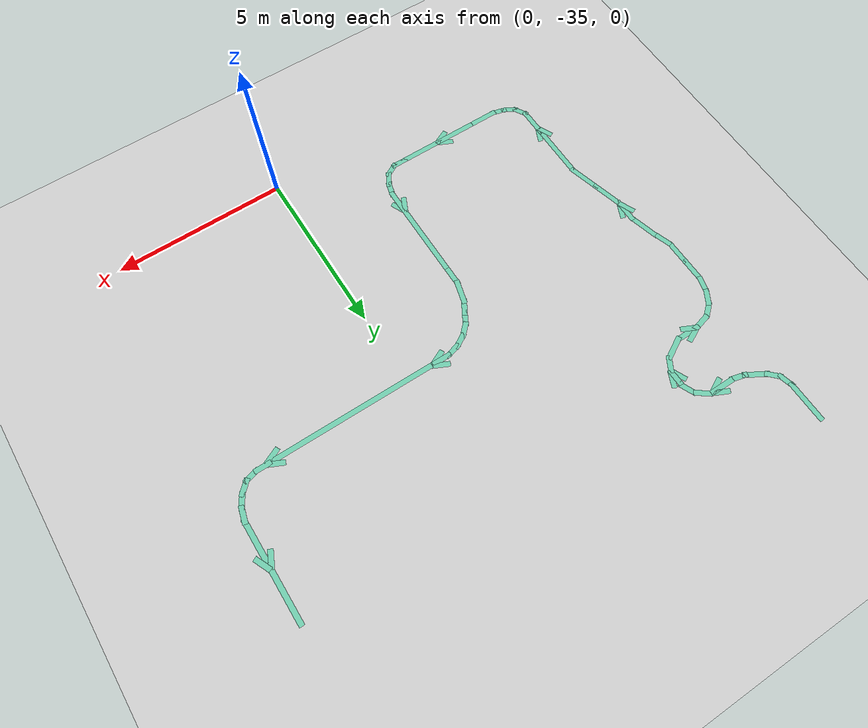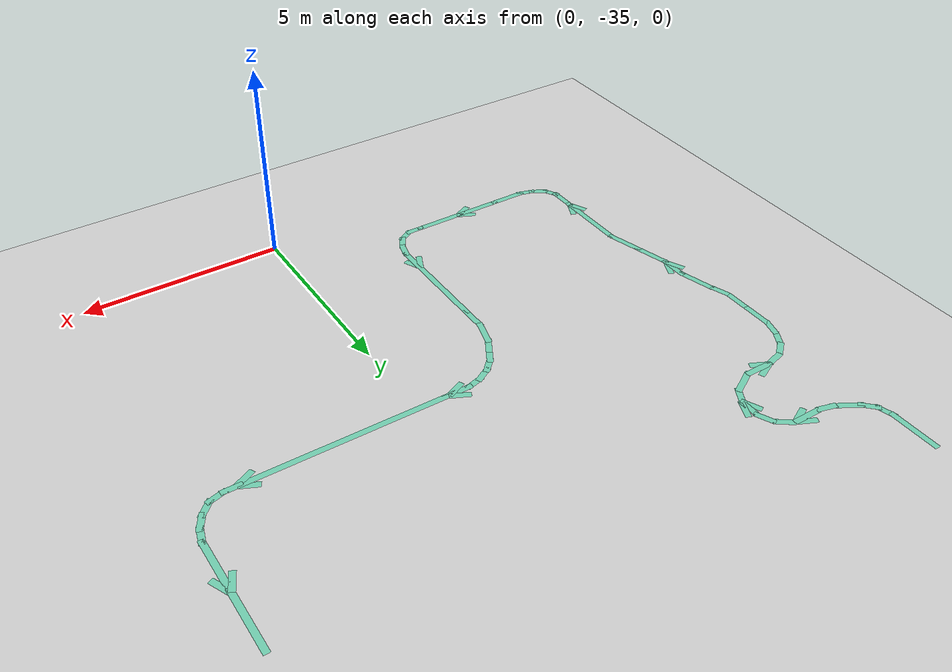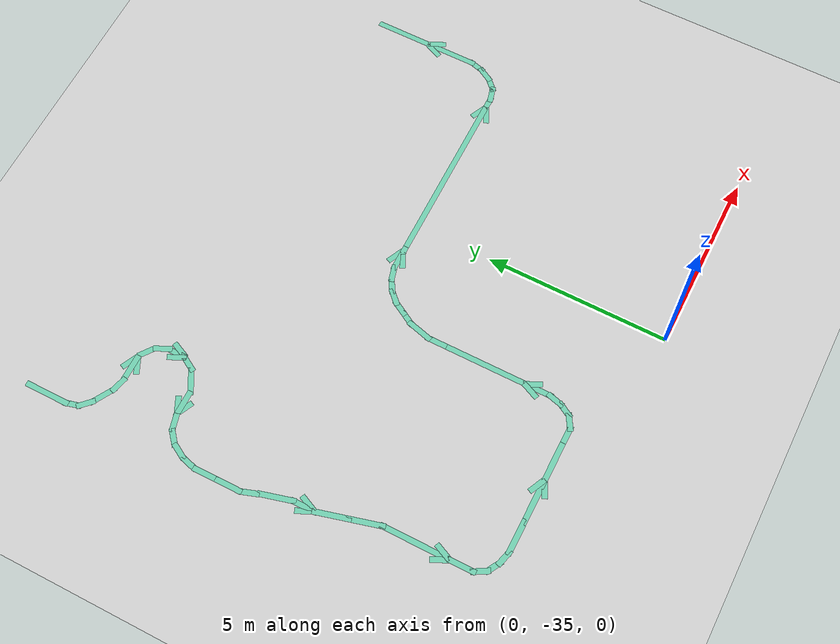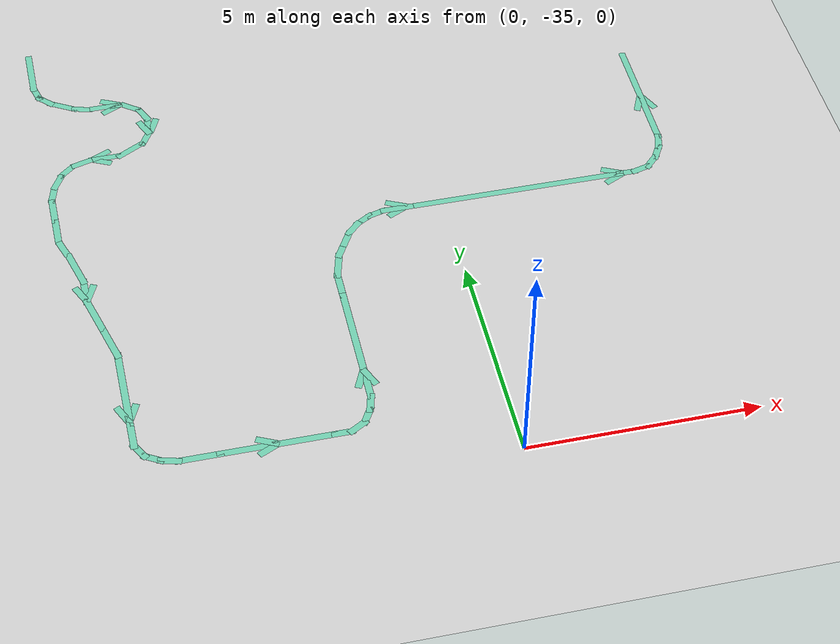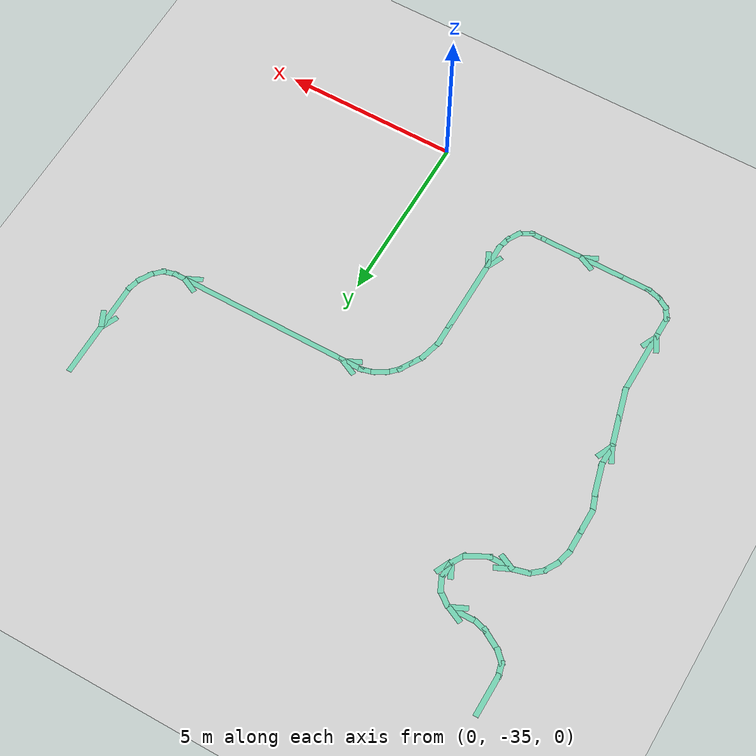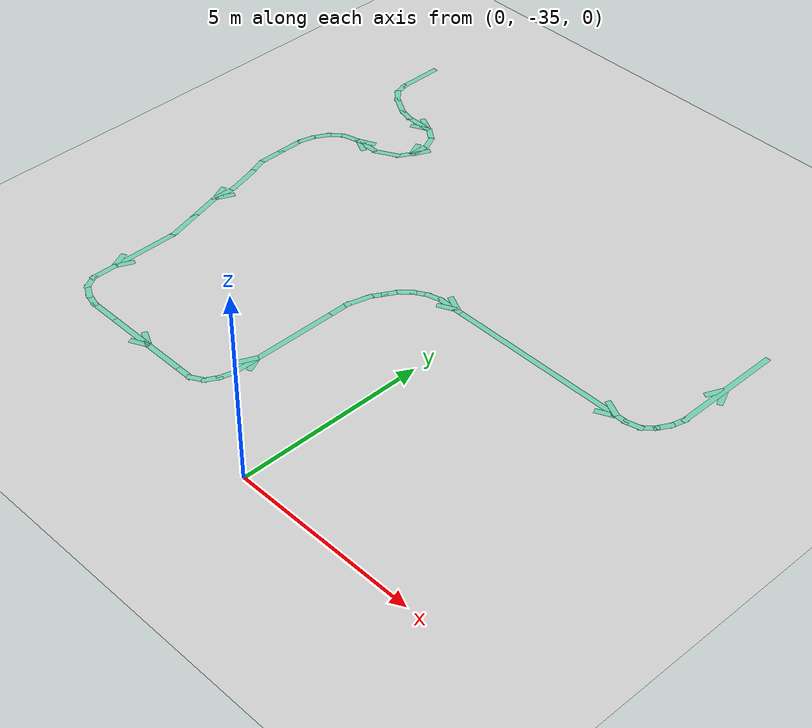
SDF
<sdf version="1.6">
 <world name="world">
  <gravity>0 0 -9.8</gravity>
  <physics name="default_physics" default="0" type="ode">
   <max_step_size>0.0010</max_step_size>
   <real_time_factor>1</real_time_factor>
   <real_time_update_rate>1000</real_time_update_rate>
  </physics>
  <scene><ambient>0.6 0.6 0.6 1</ambient><background>0.4 0.4 0.4 1</background><shadows>0</shadows></scene>
  <light name="sun" type="directional">
   <pose>0 0 10 0 -0 0</pose>
   <diffuse>0.8 0.8 0.8 1</diffuse>
   <specular>0.2 0.2 0.2 1</specular>
   <attenuation>
    <range>1000</range>
    <constant>0.9</constant>
    <linear>0.01</linear>
    <quadratic>0.001</quadratic>
   </attenuation>
   <direction>-0.5 0.1 -0.9</direction>
  </light>
  <model name="ground_plane">
   <static>1</static>
   <link name="link">
    <collision name="collision">
     <geometry><plane><normal>0 0 1</normal><size>100 100</size></plane></geometry>
     <surface><friction><ode><mu>100</mu><mu2>50</mu2></ode></friction></surface>
    </collision>
    <visual name="visual">
     <cast_shadows>0</cast_shadows>
     <geometry><plane><normal>0 0 1</normal><size>100 100</size></plane></geometry>
     <material>
      <script><uri>file://media/materials/scripts/gazebo.material</uri><name>Gazebo/Grey</name></script>
     </material>
    </visual>
   </link>
   <pose>0 0 -0.1 0 -0 0</pose>
  </model>
  <magnetic_field>6e-06 2.3e-05 -4.2e-05</magnetic_field>
  <atmosphere type="adiabatic"/>
  <spherical_coordinates>
   <surface_model>EARTH_WGS84</surface_model>
   <latitude_deg>0</latitude_deg>
   <longitude_deg>0</longitude_deg>
   <elevation>0</elevation>
   <heading_deg>0</heading_deg>
  </spherical_coordinates>
  <model name="path_hospital">
   <link name="Wall_10">
    <pose>6.85995 0.436094 0 0 0 -1.8326</pose>
    <visual name="Wall_10_Visual">
     <geometry><box><size>0.5 0.15 0</size></box></geometry>
     <material>
      <script><uri>file://media/materials/scripts/gazebo.material</uri><name>Gazebo/Grey</name></script>
      <ambient>0.435294 0.796078 0.67451 1</ambient>
      <shader type="pixel"/>
     </material>
     <meta><layer>0</layer></meta>
    </visual>
    <collision name="Wall_10_Collision">
     <geometry><box><size>0.5 0.15 0</size></box></geometry>
     <surface>
      <friction>
       <ode><mu>1</mu><mu2>1</mu2><fdir1>0 0 0</fdir1><slip1>0</slip1><slip2>0</slip2></ode>
       <torsional>
        <coefficient>1</coefficient>
        <patch_radius>0</patch_radius>
        <surface_radius>0</surface_radius>
        <use_patch_radius>1</use_patch_radius>
        <ode><slip>0</slip></ode>
       </torsional>
      </friction>
      <bounce><restitution_coefficient>0</restitution_coefficient><threshold>1e+06</threshold></bounce>
      <contact>
       <collide_without_contact>0</collide_without_contact>
       <collide_without_contact_bitmask>1</collide_without_contact_bitmask>
       <collide_bitmask>1</collide_bitmask>
       <ode>
        <soft_cfm>0</soft_cfm>
        <soft_erp>0.2</soft_erp>
        <kp>1e+13</kp>
        <kd>1</kd>
        <max_vel>0.01</max_vel>
        <min_depth>0</min_depth>
       </ode>
       <bullet>
        <split_impulse>1</split_impulse>
        <split_impulse_penetration_threshold>-0.01</split_impulse_penetration_threshold>
        <soft_cfm>0</soft_cfm>
        <soft_erp>0.2</soft_erp>
        <kp>1e+13</kp>
        <kd>1</kd>
       </bullet>
      </contact>
     </surface>
    </collision>
   </link>
   <link name="Wall_11">
    <pose>6.72715 0.115501 0 0 0 -2.0944</pose>
    <visual name="Wall_11_Visual">
     <geometry><box><size>0.5 0.15 0</size></box></geometry>
     <material>
      <script><uri>file://media/materials/scripts/gazebo.material</uri><name>Gazebo/Grey</name></script>
      <ambient>0.435294 0.796078 0.67451 1</ambient>
      <shader type="pixel"/>
     </material>
     <meta><layer>0</layer></meta>
    </visual>
    <collision name="Wall_11_Collision">
     <geometry><box><size>0.5 0.15 0</size></box></geometry>
     <surface>
      <friction>
       <ode><mu>1</mu><mu2>1</mu2><fdir1>0 0 0</fdir1><slip1>0</slip1><slip2>0</slip2></ode>
       <torsional>
        <coefficient>1</coefficient>
        <patch_radius>0</patch_radius>
        <surface_radius>0</surface_radius>
        <use_patch_radius>1</use_patch_radius>
        <ode><slip>0</slip></ode>
       </torsional>
      </friction>
      <bounce><restitution_coefficient>0</restitution_coefficient><threshold>1e+06</threshold></bounce>
      <contact>
       <collide_without_contact>0</collide_without_contact>
       <collide_without_contact_bitmask>1</collide_without_contact_bitmask>
       <collide_bitmask>1</collide_bitmask>
       <ode>
        <soft_cfm>0</soft_cfm>
        <soft_erp>0.2</soft_erp>
        <kp>1e+13</kp>
        <kd>1</kd>
        <max_vel>0.01</max_vel>
        <min_depth>0</min_depth>
       </ode>
       <bullet>
        <split_impulse>1</split_impulse>
        <split_impulse_penetration_threshold>-0.01</split_impulse_penetration_threshold>
        <soft_cfm>0</soft_cfm>
        <soft_erp>0.2</soft_erp>
        <kp>1e+13</kp>
        <kd>1</kd>
       </bullet>
      </contact>
     </surface>
    </collision>
   </link>
   <link name="Wall_12">
    <pose>6.51591 -0.159796 0 0 0 -2.35619</pose>
    <visual name="Wall_12_Visual">
     <geometry><box><size>0.5 0.15 0</size></box></geometry>
     <material>
      <script><uri>file://media/materials/scripts/gazebo.material</uri><name>Gazebo/Grey</name></script>
      <ambient>0.435294 0.796078 0.67451 1</ambient>
      <shader type="pixel"/>
     </material>
     <meta><layer>0</layer></meta>
    </visual>
    <collision name="Wall_12_Collision">
     <geometry><box><size>0.5 0.15 0</size></box></geometry>
     <surface>
      <friction>
       <ode><mu>1</mu><mu2>1</mu2><fdir1>0 0 0</fdir1><slip1>0</slip1><slip2>0</slip2></ode>
       <torsional>
        <coefficient>1</coefficient>
        <patch_radius>0</patch_radius>
        <surface_radius>0</surface_radius>
        <use_patch_radius>1</use_patch_radius>
        <ode><slip>0</slip></ode>
       </torsional>
      </friction>
      <bounce><restitution_coefficient>0</restitution_coefficient><threshold>1e+06</threshold></bounce>
      <contact>
       <collide_without_contact>0</collide_without_contact>
       <collide_without_contact_bitmask>1</collide_without_contact_bitmask>
       <collide_bitmask>1</collide_bitmask>
       <ode>
        <soft_cfm>0</soft_cfm>
        <soft_erp>0.2</soft_erp>
        <kp>1e+13</kp>
        <kd>1</kd>
        <max_vel>0.01</max_vel>
        <min_depth>0</min_depth>
       </ode>
       <bullet>
        <split_impulse>1</split_impulse>
        <split_impulse_penetration_threshold>-0.01</split_impulse_penetration_threshold>
        <soft_cfm>0</soft_cfm>
        <soft_erp>0.2</soft_erp>
        <kp>1e+13</kp>
        <kd>1</kd>
       </bullet>
      </contact>
     </surface>
    </collision>
   </link>
   <link name="Wall_13">
    <pose>6.22313 -0.328833 0 0 0 -2.87979</pose>
    <visual name="Wall_13_Visual">
     <geometry><box><size>0.5 0.15 0</size></box></geometry>
     <material>
      <script><uri>file://media/materials/scripts/gazebo.material</uri><name>Gazebo/Grey</name></script>
      <ambient>0.435294 0.796078 0.67451 1</ambient>
      <shader type="pixel"/>
     </material>
     <meta><layer>0</layer></meta>
    </visual>
    <collision name="Wall_13_Collision">
     <geometry><box><size>0.5 0.15 0</size></box></geometry>
     <surface>
      <friction>
       <ode><mu>1</mu><mu2>1</mu2><fdir1>0 0 0</fdir1><slip1>0</slip1><slip2>0</slip2></ode>
       <torsional>
        <coefficient>1</coefficient>
        <patch_radius>0</patch_radius>
        <surface_radius>0</surface_radius>
        <use_patch_radius>1</use_patch_radius>
        <ode><slip>0</slip></ode>
       </torsional>
      </friction>
      <bounce><restitution_coefficient>0</restitution_coefficient><threshold>1e+06</threshold></bounce>
      <contact>
       <collide_without_contact>0</collide_without_contact>
       <collide_without_contact_bitmask>1</collide_without_contact_bitmask>
       <collide_bitmask>1</collide_bitmask>
       <ode>
        <soft_cfm>0</soft_cfm>
        <soft_erp>0.2</soft_erp>
        <kp>1e+13</kp>
        <kd>1</kd>
        <max_vel>0.01</max_vel>
        <min_depth>0</min_depth>
       </ode>
       <bullet>
        <split_impulse>1</split_impulse>
        <split_impulse_penetration_threshold>-0.01</split_impulse_penetration_threshold>
        <soft_cfm>0</soft_cfm>
        <soft_erp>0.2</soft_erp>
        <kp>1e+13</kp>
        <kd>1</kd>
       </bullet>
      </contact>
     </surface>
    </collision>
   </link>
   <link name="Wall_14">
    <pose>5.87909 -0.374126 0 0 -0 3.14159</pose>
    <visual name="Wall_14_Visual">
     <geometry><box><size>0.5 0.15 0</size></box></geometry>
     <material>
      <script><uri>file://media/materials/scripts/gazebo.material</uri><name>Gazebo/Grey</name></script>
      <ambient>0.435294 0.796078 0.67451 1</ambient>
      <shader type="pixel"/>
     </material>
     <meta><layer>0</layer></meta>
    </visual>
    <collision name="Wall_14_Collision">
     <geometry><box><size>0.5 0.15 0</size></box></geometry>
     <surface>
      <friction>
       <ode><mu>1</mu><mu2>1</mu2><fdir1>0 0 0</fdir1><slip1>0</slip1><slip2>0</slip2></ode>
       <torsional>
        <coefficient>1</coefficient>
        <patch_radius>0</patch_radius>
        <surface_radius>0</surface_radius>
        <use_patch_radius>1</use_patch_radius>
        <ode><slip>0</slip></ode>
       </torsional>
      </friction>
      <bounce><restitution_coefficient>0</restitution_coefficient><threshold>1e+06</threshold></bounce>
      <contact>
       <collide_without_contact>0</collide_without_contact>
       <collide_without_contact_bitmask>1</collide_without_contact_bitmask>
       <collide_bitmask>1</collide_bitmask>
       <ode>
        <soft_cfm>0</soft_cfm>
        <soft_erp>0.2</soft_erp>
        <kp>1e+13</kp>
        <kd>1</kd>
        <max_vel>0.01</max_vel>
        <min_depth>0</min_depth>
       </ode>
       <bullet>
        <split_impulse>1</split_impulse>
        <split_impulse_penetration_threshold>-0.01</split_impulse_penetration_threshold>
        <soft_cfm>0</soft_cfm>
        <soft_erp>0.2</soft_erp>
        <kp>1e+13</kp>
        <kd>1</kd>
       </bullet>
      </contact>
     </surface>
    </collision>
   </link>
   <link name="Wall_15">
    <pose>3.27909 -0.374126 0 0 -0 3.14159</pose>
    <visual name="Wall_15_Visual">
     <geometry><box><size>5 0.15 0</size></box></geometry>
     <material>
      <script><uri>file://media/materials/scripts/gazebo.material</uri><name>Gazebo/Grey</name></script>
      <ambient>0.435294 0.796078 0.67451 1</ambient>
      <shader type="pixel"/>
     </material>
     <meta><layer>0</layer></meta>
    </visual>
    <collision name="Wall_15_Collision">
     <geometry><box><size>5 0.15 0</size></box></geometry>
     <surface>
      <friction>
       <ode><mu>1</mu><mu2>1</mu2><fdir1>0 0 0</fdir1><slip1>0</slip1><slip2>0</slip2></ode>
       <torsional>
        <coefficient>1</coefficient>
        <patch_radius>0</patch_radius>
        <surface_radius>0</surface_radius>
        <use_patch_radius>1</use_patch_radius>
        <ode><slip>0</slip></ode>
       </torsional>
      </friction>
      <bounce><restitution_coefficient>0</restitution_coefficient><threshold>1e+06</threshold></bounce>
      <contact>
       <collide_without_contact>0</collide_without_contact>
       <collide_without_contact_bitmask>1</collide_without_contact_bitmask>
       <collide_bitmask>1</collide_bitmask>
       <ode>
        <soft_cfm>0</soft_cfm>
        <soft_erp>0.2</soft_erp>
        <kp>1e+13</kp>
        <kd>1</kd>
        <max_vel>0.01</max_vel>
        <min_depth>0</min_depth>
       </ode>
       <bullet>
        <split_impulse>1</split_impulse>
        <split_impulse_penetration_threshold>-0.01</split_impulse_penetration_threshold>
        <soft_cfm>0</soft_cfm>
        <soft_erp>0.2</soft_erp>
        <kp>1e+13</kp>
        <kd>1</kd>
       </bullet>
      </contact>
     </surface>
    </collision>
   </link>
   <link name="Wall_16">
    <pose>0.554091 -0.374126 0 0 -0 3.14159</pose>
    <visual name="Wall_16_Visual">
     <geometry><box><size>0.75 0.15 0</size></box></geometry>
     <material>
      <script><uri>file://media/materials/scripts/gazebo.material</uri><name>Gazebo/Grey</name></script>
      <ambient>0.435294 0.796078 0.67451 1</ambient>
      <shader type="pixel"/>
     </material>
     <meta><layer>0</layer></meta>
    </visual>
    <collision name="Wall_16_Collision">
     <geometry><box><size>0.75 0.15 0</size></box></geometry>
     <surface>
      <friction>
       <ode><mu>1</mu><mu2>1</mu2><fdir1>0 0 0</fdir1><slip1>0</slip1><slip2>0</slip2></ode>
       <torsional>
        <coefficient>1</coefficient>
        <patch_radius>0</patch_radius>
        <surface_radius>0</surface_radius>
        <use_patch_radius>1</use_patch_radius>
        <ode><slip>0</slip></ode>
       </torsional>
      </friction>
      <bounce><restitution_coefficient>0</restitution_coefficient><threshold>1e+06</threshold></bounce>
      <contact>
       <collide_without_contact>0</collide_without_contact>
       <collide_without_contact_bitmask>1</collide_without_contact_bitmask>
       <collide_bitmask>1</collide_bitmask>
       <ode>
        <soft_cfm>0</soft_cfm>
        <soft_erp>0.2</soft_erp>
        <kp>1e+13</kp>
        <kd>1</kd>
        <max_vel>0.01</max_vel>
        <min_depth>0</min_depth>
       </ode>
       <bullet>
        <split_impulse>1</split_impulse>
        <split_impulse_penetration_threshold>-0.01</split_impulse_penetration_threshold>
        <soft_cfm>0</soft_cfm>
        <soft_erp>0.2</soft_erp>
        <kp>1e+13</kp>
        <kd>1</kd>
       </bullet>
      </contact>
     </surface>
    </collision>
   </link>
   <link name="Wall_17">
    <pose>0.085054 -0.41942 0 0 0 -2.87979</pose>
    <visual name="Wall_17_Visual">
     <geometry><box><size>0.5 0.15 0</size></box></geometry>
     <material>
      <script><uri>file://media/materials/scripts/gazebo.material</uri><name>Gazebo/Grey</name></script>
      <ambient>0.435294 0.796078 0.67451 1</ambient>
      <shader type="pixel"/>
     </material>
     <meta><layer>0</layer></meta>
    </visual>
    <collision name="Wall_17_Collision">
     <geometry><box><size>0.5 0.15 0</size></box></geometry>
     <surface>
      <friction>
       <ode><mu>1</mu><mu2>1</mu2><fdir1>0 0 0</fdir1><slip1>0</slip1><slip2>0</slip2></ode>
       <torsional>
        <coefficient>1</coefficient>
        <patch_radius>0</patch_radius>
        <surface_radius>0</surface_radius>
        <use_patch_radius>1</use_patch_radius>
        <ode><slip>0</slip></ode>
       </torsional>
      </friction>
      <bounce><restitution_coefficient>0</restitution_coefficient><threshold>1e+06</threshold></bounce>
      <contact>
       <collide_without_contact>0</collide_without_contact>
       <collide_without_contact_bitmask>1</collide_without_contact_bitmask>
       <collide_bitmask>1</collide_bitmask>
       <ode>
        <soft_cfm>0</soft_cfm>
        <soft_erp>0.2</soft_erp>
        <kp>1e+13</kp>
        <kd>1</kd>
        <max_vel>0.01</max_vel>
        <min_depth>0</min_depth>
       </ode>
       <bullet>
        <split_impulse>1</split_impulse>
        <split_impulse_penetration_threshold>-0.01</split_impulse_penetration_threshold>
        <soft_cfm>0</soft_cfm>
        <soft_erp>0.2</soft_erp>
        <kp>1e+13</kp>
        <kd>1</kd>
       </bullet>
      </contact>
     </surface>
    </collision>
   </link>
   <link name="Wall_18">
    <pose>-0.235537 -0.552214 0 0 0 -2.61799</pose>
    <visual name="Wall_18_Visual">
     <geometry><box><size>0.5 0.15 0</size></box></geometry>
     <material>
      <script><uri>file://media/materials/scripts/gazebo.material</uri><name>Gazebo/Grey</name></script>
      <ambient>0.435294 0.796078 0.67451 1</ambient>
      <shader type="pixel"/>
     </material>
     <meta><layer>0</layer></meta>
    </visual>
    <collision name="Wall_18_Collision">
     <geometry><box><size>0.5 0.15 0</size></box></geometry>
     <surface>
      <friction>
       <ode><mu>1</mu><mu2>1</mu2><fdir1>0 0 0</fdir1><slip1>0</slip1><slip2>0</slip2></ode>
       <torsional>
        <coefficient>1</coefficient>
        <patch_radius>0</patch_radius>
        <surface_radius>0</surface_radius>
        <use_patch_radius>1</use_patch_radius>
        <ode><slip>0</slip></ode>
       </torsional>
      </friction>
      <bounce><restitution_coefficient>0</restitution_coefficient><threshold>1e+06</threshold></bounce>
      <contact>
       <collide_without_contact>0</collide_without_contact>
       <collide_without_contact_bitmask>1</collide_without_contact_bitmask>
       <collide_bitmask>1</collide_bitmask>
       <ode>
        <soft_cfm>0</soft_cfm>
        <soft_erp>0.2</soft_erp>
        <kp>1e+13</kp>
        <kd>1</kd>
        <max_vel>0.01</max_vel>
        <min_depth>0</min_depth>
       </ode>
       <bullet>
        <split_impulse>1</split_impulse>
        <split_impulse_penetration_threshold>-0.01</split_impulse_penetration_threshold>
        <soft_cfm>0</soft_cfm>
        <soft_erp>0.2</soft_erp>
        <kp>1e+13</kp>
        <kd>1</kd>
       </bullet>
      </contact>
     </surface>
    </collision>
   </link>
   <link name="Wall_19">
    <pose>-0.510835 -0.763456 0 0 0 -2.35619</pose>
    <visual name="Wall_19_Visual">
     <geometry><box><size>0.5 0.15 0</size></box></geometry>
     <material>
      <script><uri>file://media/materials/scripts/gazebo.material</uri><name>Gazebo/Grey</name></script>
      <ambient>0.435294 0.796078 0.67451 1</ambient>
      <shader type="pixel"/>
     </material>
     <meta><layer>0</layer></meta>
    </visual>
    <collision name="Wall_19_Collision">
     <geometry><box><size>0.5 0.15 0</size></box></geometry>
     <surface>
      <friction>
       <ode><mu>1</mu><mu2>1</mu2><fdir1>0 0 0</fdir1><slip1>0</slip1><slip2>0</slip2></ode>
       <torsional>
        <coefficient>1</coefficient>
        <patch_radius>0</patch_radius>
        <surface_radius>0</surface_radius>
        <use_patch_radius>1</use_patch_radius>
        <ode><slip>0</slip></ode>
       </torsional>
      </friction>
      <bounce><restitution_coefficient>0</restitution_coefficient><threshold>1e+06</threshold></bounce>
      <contact>
       <collide_without_contact>0</collide_without_contact>
       <collide_without_contact_bitmask>1</collide_without_contact_bitmask>
       <collide_bitmask>1</collide_bitmask>
       <ode>
        <soft_cfm>0</soft_cfm>
        <soft_erp>0.2</soft_erp>
        <kp>1e+13</kp>
        <kd>1</kd>
        <max_vel>0.01</max_vel>
        <min_depth>0</min_depth>
       </ode>
       <bullet>
        <split_impulse>1</split_impulse>
        <split_impulse_penetration_threshold>-0.01</split_impulse_penetration_threshold>
        <soft_cfm>0</soft_cfm>
        <soft_erp>0.2</soft_erp>
        <kp>1e+13</kp>
        <kd>1</kd>
       </bullet>
      </contact>
     </surface>
    </collision>
   </link>
   <link name="Wall_20">
    <pose>-0.722079 -1.03876 0 0 0 -2.0944</pose>
    <visual name="Wall_20_Visual">
     <geometry><box><size>0.5 0.15 0</size></box></geometry>
     <material>
      <script><uri>file://media/materials/scripts/gazebo.material</uri><name>Gazebo/Grey</name></script>
      <ambient>0.435294 0.796078 0.67451 1</ambient>
      <shader type="pixel"/>
     </material>
     <meta><layer>0</layer></meta>
    </visual>
    <collision name="Wall_20_Collision">
     <geometry><box><size>0.5 0.15 0</size></box></geometry>
     <surface>
      <friction>
       <ode><mu>1</mu><mu2>1</mu2><fdir1>0 0 0</fdir1><slip1>0</slip1><slip2>0</slip2></ode>
       <torsional>
        <coefficient>1</coefficient>
        <patch_radius>0</patch_radius>
        <surface_radius>0</surface_radius>
        <use_patch_radius>1</use_patch_radius>
        <ode><slip>0</slip></ode>
       </torsional>
      </friction>
      <bounce><restitution_coefficient>0</restitution_coefficient><threshold>1e+06</threshold></bounce>
      <contact>
       <collide_without_contact>0</collide_without_contact>
       <collide_without_contact_bitmask>1</collide_without_contact_bitmask>
       <collide_bitmask>1</collide_bitmask>
       <ode>
        <soft_cfm>0</soft_cfm>
        <soft_erp>0.2</soft_erp>
        <kp>1e+13</kp>
        <kd>1</kd>
        <max_vel>0.01</max_vel>
        <min_depth>0</min_depth>
       </ode>
       <bullet>
        <split_impulse>1</split_impulse>
        <split_impulse_penetration_threshold>-0.01</split_impulse_penetration_threshold>
        <soft_cfm>0</soft_cfm>
        <soft_erp>0.2</soft_erp>
        <kp>1e+13</kp>
        <kd>1</kd>
       </bullet>
      </contact>
     </surface>
    </collision>
   </link>
   <link name="Wall_21">
    <pose>-0.897079 -1.34186 0 0 0 -2.0944</pose>
    <visual name="Wall_21_Visual">
     <geometry><box><size>0.5 0.15 0</size></box></geometry>
     <material>
      <script><uri>file://media/materials/scripts/gazebo.material</uri><name>Gazebo/Grey</name></script>
      <ambient>0.435294 0.796078 0.67451 1</ambient>
      <shader type="pixel"/>
     </material>
     <meta><layer>0</layer></meta>
    </visual>
    <collision name="Wall_21_Collision">
     <geometry><box><size>0.5 0.15 0</size></box></geometry>
     <surface>
      <friction>
       <ode><mu>1</mu><mu2>1</mu2><fdir1>0 0 0</fdir1><slip1>0</slip1><slip2>0</slip2></ode>
       <torsional>
        <coefficient>1</coefficient>
        <patch_radius>0</patch_radius>
        <surface_radius>0</surface_radius>
        <use_patch_radius>1</use_patch_radius>
        <ode><slip>0</slip></ode>
       </torsional>
      </friction>
      <bounce><restitution_coefficient>0</restitution_coefficient><threshold>1e+06</threshold></bounce>
      <contact>
       <collide_without_contact>0</collide_without_contact>
       <collide_without_contact_bitmask>1</collide_without_contact_bitmask>
       <collide_bitmask>1</collide_bitmask>
       <ode>
        <soft_cfm>0</soft_cfm>
        <soft_erp>0.2</soft_erp>
        <kp>1e+13</kp>
        <kd>1</kd>
        <max_vel>0.01</max_vel>
        <min_depth>0</min_depth>
       </ode>
       <bullet>
        <split_impulse>1</split_impulse>
        <split_impulse_penetration_threshold>-0.01</split_impulse_penetration_threshold>
        <soft_cfm>0</soft_cfm>
        <soft_erp>0.2</soft_erp>
        <kp>1e+13</kp>
        <kd>1</kd>
       </bullet>
      </contact>
     </surface>
    </collision>
   </link>
   <link name="Wall_22">
    <pose>-1.06222 -1.7832 0 0 0 -1.8326</pose>
    <visual name="Wall_22_Visual">
     <geometry><box><size>0.75 0.15 0</size></box></geometry>
     <material>
      <script><uri>file://media/materials/scripts/gazebo.material</uri><name>Gazebo/Grey</name></script>
      <ambient>0.435294 0.796078 0.67451 1</ambient>
      <shader type="pixel"/>
     </material>
     <meta><layer>0</layer></meta>
    </visual>
    <collision name="Wall_22_Collision">
     <geometry><box><size>0.75 0.15 0</size></box></geometry>
     <surface>
      <friction>
       <ode><mu>1</mu><mu2>1</mu2><fdir1>0 0 0</fdir1><slip1>0</slip1><slip2>0</slip2></ode>
       <torsional>
        <coefficient>1</coefficient>
        <patch_radius>0</patch_radius>
        <surface_radius>0</surface_radius>
        <use_patch_radius>1</use_patch_radius>
        <ode><slip>0</slip></ode>
       </torsional>
      </friction>
      <bounce><restitution_coefficient>0</restitution_coefficient><threshold>1e+06</threshold></bounce>
      <contact>
       <collide_without_contact>0</collide_without_contact>
       <collide_without_contact_bitmask>1</collide_without_contact_bitmask>
       <collide_bitmask>1</collide_bitmask>
       <ode>
        <soft_cfm>0</soft_cfm>
        <soft_erp>0.2</soft_erp>
        <kp>1e+13</kp>
        <kd>1</kd>
        <max_vel>0.01</max_vel>
        <min_depth>0</min_depth>
       </ode>
       <bullet>
        <split_impulse>1</split_impulse>
        <split_impulse_penetration_threshold>-0.01</split_impulse_penetration_threshold>
        <soft_cfm>0</soft_cfm>
        <soft_erp>0.2</soft_erp>
        <kp>1e+13</kp>
        <kd>1</kd>
       </bullet>
      </contact>
     </surface>
    </collision>
   </link>
   <link name="Wall_23">
    <pose>-1.13987 -2.37297 0 0 0 -1.5708</pose>
    <visual name="Wall_23_Visual">
     <geometry><box><size>0.75 0.15 0</size></box></geometry>
     <material>
      <script><uri>file://media/materials/scripts/gazebo.material</uri><name>Gazebo/Grey</name></script>
      <ambient>0.435294 0.796078 0.67451 1</ambient>
      <shader type="pixel"/>
     </material>
     <meta><layer>0</layer></meta>
    </visual>
    <collision name="Wall_23_Collision">
     <geometry><box><size>0.75 0.15 0</size></box></geometry>
     <surface>
      <friction>
       <ode><mu>1</mu><mu2>1</mu2><fdir1>0 0 0</fdir1><slip1>0</slip1><slip2>0</slip2></ode>
       <torsional>
        <coefficient>1</coefficient>
        <patch_radius>0</patch_radius>
        <surface_radius>0</surface_radius>
        <use_patch_radius>1</use_patch_radius>
        <ode><slip>0</slip></ode>
       </torsional>
      </friction>
      <bounce><restitution_coefficient>0</restitution_coefficient><threshold>1e+06</threshold></bounce>
      <contact>
       <collide_without_contact>0</collide_without_contact>
       <collide_without_contact_bitmask>1</collide_without_contact_bitmask>
       <collide_bitmask>1</collide_bitmask>
       <ode>
        <soft_cfm>0</soft_cfm>
        <soft_erp>0.2</soft_erp>
        <kp>1e+13</kp>
        <kd>1</kd>
        <max_vel>0.01</max_vel>
        <min_depth>0</min_depth>
       </ode>
       <bullet>
        <split_impulse>1</split_impulse>
        <split_impulse_penetration_threshold>-0.01</split_impulse_penetration_threshold>
        <soft_cfm>0</soft_cfm>
        <soft_erp>0.2</soft_erp>
        <kp>1e+13</kp>
        <kd>1</kd>
       </bullet>
      </contact>
     </surface>
    </collision>
   </link>
   <link name="Wall_24">
    <pose>-1.13987 -4.09797 0 0 0 -1.5708</pose>
    <visual name="Wall_24_Visual">
     <geometry><box><size>3 0.15 0</size></box></geometry>
     <material>
      <script><uri>file://media/materials/scripts/gazebo.material</uri><name>Gazebo/Grey</name></script>
      <ambient>0.435294 0.796078 0.67451 1</ambient>
      <shader type="pixel"/>
     </material>
     <meta><layer>0</layer></meta>
    </visual>
    <collision name="Wall_24_Collision">
     <geometry><box><size>3 0.15 0</size></box></geometry>
     <surface>
      <friction>
       <ode><mu>1</mu><mu2>1</mu2><fdir1>0 0 0</fdir1><slip1>0</slip1><slip2>0</slip2></ode>
       <torsional>
        <coefficient>1</coefficient>
        <patch_radius>0</patch_radius>
        <surface_radius>0</surface_radius>
        <use_patch_radius>1</use_patch_radius>
        <ode><slip>0</slip></ode>
       </torsional>
      </friction>
      <bounce><restitution_coefficient>0</restitution_coefficient><threshold>1e+06</threshold></bounce>
      <contact>
       <collide_without_contact>0</collide_without_contact>
       <collide_without_contact_bitmask>1</collide_without_contact_bitmask>
       <collide_bitmask>1</collide_bitmask>
       <ode>
        <soft_cfm>0</soft_cfm>
        <soft_erp>0.2</soft_erp>
        <kp>1e+13</kp>
        <kd>1</kd>
        <max_vel>0.01</max_vel>
        <min_depth>0</min_depth>
       </ode>
       <bullet>
        <split_impulse>1</split_impulse>
        <split_impulse_penetration_threshold>-0.01</split_impulse_penetration_threshold>
        <soft_cfm>0</soft_cfm>
        <soft_erp>0.2</soft_erp>
        <kp>1e+13</kp>
        <kd>1</kd>
       </bullet>
      </contact>
     </surface>
    </collision>
   </link>
   <link name="Wall_25">
    <pose>-1.18516 -5.69201 0 0 0 -1.8326</pose>
    <visual name="Wall_25_Visual">
     <geometry><box><size>0.5 0.15 0</size></box></geometry>
     <material>
      <script><uri>file://media/materials/scripts/gazebo.material</uri><name>Gazebo/Grey</name></script>
      <ambient>0.435294 0.796078 0.67451 1</ambient>
      <shader type="pixel"/>
     </material>
     <meta><layer>0</layer></meta>
    </visual>
    <collision name="Wall_25_Collision">
     <geometry><box><size>0.5 0.15 0</size></box></geometry>
     <surface>
      <friction>
       <ode><mu>1</mu><mu2>1</mu2><fdir1>0 0 0</fdir1><slip1>0</slip1><slip2>0</slip2></ode>
       <torsional>
        <coefficient>1</coefficient>
        <patch_radius>0</patch_radius>
        <surface_radius>0</surface_radius>
        <use_patch_radius>1</use_patch_radius>
        <ode><slip>0</slip></ode>
       </torsional>
      </friction>
      <bounce><restitution_coefficient>0</restitution_coefficient><threshold>1e+06</threshold></bounce>
      <contact>
       <collide_without_contact>0</collide_without_contact>
       <collide_without_contact_bitmask>1</collide_without_contact_bitmask>
       <collide_bitmask>1</collide_bitmask>
       <ode>
        <soft_cfm>0</soft_cfm>
        <soft_erp>0.2</soft_erp>
        <kp>1e+13</kp>
        <kd>1</kd>
        <max_vel>0.01</max_vel>
        <min_depth>0</min_depth>
       </ode>
       <bullet>
        <split_impulse>1</split_impulse>
        <split_impulse_penetration_threshold>-0.01</split_impulse_penetration_threshold>
        <soft_cfm>0</soft_cfm>
        <soft_erp>0.2</soft_erp>
        <kp>1e+13</kp>
        <kd>1</kd>
       </bullet>
      </contact>
     </surface>
    </collision>
   </link>
   <link name="Wall_26">
    <pose>-1.31796 -6.0126 0 0 0 -2.0944</pose>
    <visual name="Wall_26_Visual">
     <geometry><box><size>0.5 0.15 0</size></box></geometry>
     <material>
      <script><uri>file://media/materials/scripts/gazebo.material</uri><name>Gazebo/Grey</name></script>
      <ambient>0.435294 0.796078 0.67451 1</ambient>
      <shader type="pixel"/>
     </material>
     <meta><layer>0</layer></meta>
    </visual>
    <collision name="Wall_26_Collision">
     <geometry><box><size>0.5 0.15 0</size></box></geometry>
     <surface>
      <friction>
       <ode><mu>1</mu><mu2>1</mu2><fdir1>0 0 0</fdir1><slip1>0</slip1><slip2>0</slip2></ode>
       <torsional>
        <coefficient>1</coefficient>
        <patch_radius>0</patch_radius>
        <surface_radius>0</surface_radius>
        <use_patch_radius>1</use_patch_radius>
        <ode><slip>0</slip></ode>
       </torsional>
      </friction>
      <bounce><restitution_coefficient>0</restitution_coefficient><threshold>1e+06</threshold></bounce>
      <contact>
       <collide_without_contact>0</collide_without_contact>
       <collide_without_contact_bitmask>1</collide_without_contact_bitmask>
       <collide_bitmask>1</collide_bitmask>
       <ode>
        <soft_cfm>0</soft_cfm>
        <soft_erp>0.2</soft_erp>
        <kp>1e+13</kp>
        <kd>1</kd>
        <max_vel>0.01</max_vel>
        <min_depth>0</min_depth>
       </ode>
       <bullet>
        <split_impulse>1</split_impulse>
        <split_impulse_penetration_threshold>-0.01</split_impulse_penetration_threshold>
        <soft_cfm>0</soft_cfm>
        <soft_erp>0.2</soft_erp>
        <kp>1e+13</kp>
        <kd>1</kd>
       </bullet>
      </contact>
     </surface>
    </collision>
   </link>
   <link name="Wall_27">
    <pose>-1.55701 -6.25166 0 0 0 -2.61799</pose>
    <visual name="Wall_27_Visual">
     <geometry><box><size>0.5 0.15 0</size></box></geometry>
     <material>
      <script><uri>file://media/materials/scripts/gazebo.material</uri><name>Gazebo/Grey</name></script>
      <ambient>0.435294 0.796078 0.67451 1</ambient>
      <shader type="pixel"/>
     </material>
     <meta><layer>0</layer></meta>
    </visual>
    <collision name="Wall_27_Collision">
     <geometry><box><size>0.5 0.15 0</size></box></geometry>
     <surface>
      <friction>
       <ode><mu>1</mu><mu2>1</mu2><fdir1>0 0 0</fdir1><slip1>0</slip1><slip2>0</slip2></ode>
       <torsional>
        <coefficient>1</coefficient>
        <patch_radius>0</patch_radius>
        <surface_radius>0</surface_radius>
        <use_patch_radius>1</use_patch_radius>
        <ode><slip>0</slip></ode>
       </torsional>
      </friction>
      <bounce><restitution_coefficient>0</restitution_coefficient><threshold>1e+06</threshold></bounce>
      <contact>
       <collide_without_contact>0</collide_without_contact>
       <collide_without_contact_bitmask>1</collide_without_contact_bitmask>
       <collide_bitmask>1</collide_bitmask>
       <ode>
        <soft_cfm>0</soft_cfm>
        <soft_erp>0.2</soft_erp>
        <kp>1e+13</kp>
        <kd>1</kd>
        <max_vel>0.01</max_vel>
        <min_depth>0</min_depth>
       </ode>
       <bullet>
        <split_impulse>1</split_impulse>
        <split_impulse_penetration_threshold>-0.01</split_impulse_penetration_threshold>
        <soft_cfm>0</soft_cfm>
        <soft_erp>0.2</soft_erp>
        <kp>1e+13</kp>
        <kd>1</kd>
       </bullet>
      </contact>
     </surface>
    </collision>
   </link>
   <link name="Wall_28">
    <pose>-1.88357 -6.33915 0 0 -0 3.14159</pose>
    <visual name="Wall_28_Visual">
     <geometry><box><size>0.5 0.15 0</size></box></geometry>
     <material>
      <script><uri>file://media/materials/scripts/gazebo.material</uri><name>Gazebo/Grey</name></script>
      <ambient>0.435294 0.796078 0.67451 1</ambient>
      <shader type="pixel"/>
     </material>
     <meta><layer>0</layer></meta>
    </visual>
    <collision name="Wall_28_Collision">
     <geometry><box><size>0.5 0.15 0</size></box></geometry>
     <surface>
      <friction>
       <ode><mu>1</mu><mu2>1</mu2><fdir1>0 0 0</fdir1><slip1>0</slip1><slip2>0</slip2></ode>
       <torsional>
        <coefficient>1</coefficient>
        <patch_radius>0</patch_radius>
        <surface_radius>0</surface_radius>
        <use_patch_radius>1</use_patch_radius>
        <ode><slip>0</slip></ode>
       </torsional>
      </friction>
      <bounce><restitution_coefficient>0</restitution_coefficient><threshold>1e+06</threshold></bounce>
      <contact>
       <collide_without_contact>0</collide_without_contact>
       <collide_without_contact_bitmask>1</collide_without_contact_bitmask>
       <collide_bitmask>1</collide_bitmask>
       <ode>
        <soft_cfm>0</soft_cfm>
        <soft_erp>0.2</soft_erp>
        <kp>1e+13</kp>
        <kd>1</kd>
        <max_vel>0.01</max_vel>
        <min_depth>0</min_depth>
       </ode>
       <bullet>
        <split_impulse>1</split_impulse>
        <split_impulse_penetration_threshold>-0.01</split_impulse_penetration_threshold>
        <soft_cfm>0</soft_cfm>
        <soft_erp>0.2</soft_erp>
        <kp>1e+13</kp>
        <kd>1</kd>
       </bullet>
      </contact>
     </surface>
    </collision>
   </link>
   <link name="Wall_29">
    <pose>-3.23357 -6.33915 0 0 -0 3.14159</pose>
    <visual name="Wall_29_Visual">
     <geometry><box><size>2.5 0.15 0</size></box></geometry>
     <material>
      <script><uri>file://media/materials/scripts/gazebo.material</uri><name>Gazebo/Grey</name></script>
      <ambient>0.435294 0.796078 0.67451 1</ambient>
      <shader type="pixel"/>
     </material>
     <meta><layer>0</layer></meta>
    </visual>
    <collision name="Wall_29_Collision">
     <geometry><box><size>2.5 0.15 0</size></box></geometry>
     <surface>
      <friction>
       <ode><mu>1</mu><mu2>1</mu2><fdir1>0 0 0</fdir1><slip1>0</slip1><slip2>0</slip2></ode>
       <torsional>
        <coefficient>1</coefficient>
        <patch_radius>0</patch_radius>
        <surface_radius>0</surface_radius>
        <use_patch_radius>1</use_patch_radius>
        <ode><slip>0</slip></ode>
       </torsional>
      </friction>
      <bounce><restitution_coefficient>0</restitution_coefficient><threshold>1e+06</threshold></bounce>
      <contact>
       <collide_without_contact>0</collide_without_contact>
       <collide_without_contact_bitmask>1</collide_without_contact_bitmask>
       <collide_bitmask>1</collide_bitmask>
       <ode>
        <soft_cfm>0</soft_cfm>
        <soft_erp>0.2</soft_erp>
        <kp>1e+13</kp>
        <kd>1</kd>
        <max_vel>0.01</max_vel>
        <min_depth>0</min_depth>
       </ode>
       <bullet>
        <split_impulse>1</split_impulse>
        <split_impulse_penetration_threshold>-0.01</split_impulse_penetration_threshold>
        <soft_cfm>0</soft_cfm>
        <soft_erp>0.2</soft_erp>
        <kp>1e+13</kp>
        <kd>1</kd>
       </bullet>
      </contact>
     </surface>
    </collision>
   </link>
   <link name="Wall_31">
    <pose>-4.83357 -6.33915 0 0 -0 3.14159</pose>
    <visual name="Wall_31_Visual">
     <geometry><box><size>1 0.15 0</size></box></geometry>
     <material>
      <script><uri>file://media/materials/scripts/gazebo.material</uri><name>Gazebo/Grey</name></script>
      <ambient>0.435294 0.796078 0.67451 1</ambient>
      <shader type="pixel"/>
     </material>
     <meta><layer>0</layer></meta>
    </visual>
    <collision name="Wall_31_Collision">
     <geometry><box><size>1 0.15 0</size></box></geometry>
     <surface>
      <friction>
       <ode><mu>1</mu><mu2>1</mu2><fdir1>0 0 0</fdir1><slip1>0</slip1><slip2>0</slip2></ode>
       <torsional>
        <coefficient>1</coefficient>
        <patch_radius>0</patch_radius>
        <surface_radius>0</surface_radius>
        <use_patch_radius>1</use_patch_radius>
        <ode><slip>0</slip></ode>
       </torsional>
      </friction>
      <bounce><restitution_coefficient>0</restitution_coefficient><threshold>1e+06</threshold></bounce>
      <contact>
       <collide_without_contact>0</collide_without_contact>
       <collide_without_contact_bitmask>1</collide_without_contact_bitmask>
       <collide_bitmask>1</collide_bitmask>
       <ode>
        <soft_cfm>0</soft_cfm>
        <soft_erp>0.2</soft_erp>
        <kp>1e+13</kp>
        <kd>1</kd>
        <max_vel>0.01</max_vel>
        <min_depth>0</min_depth>
       </ode>
       <bullet>
        <split_impulse>1</split_impulse>
        <split_impulse_penetration_threshold>-0.01</split_impulse_penetration_threshold>
        <soft_cfm>0</soft_cfm>
        <soft_erp>0.2</soft_erp>
        <kp>1e+13</kp>
        <kd>1</kd>
       </bullet>
      </contact>
     </surface>
    </collision>
   </link>
   <link name="Wall_32">
    <pose>-5.4276 -6.29386 0 0 -0 2.87979</pose>
    <visual name="Wall_32_Visual">
     <geometry><box><size>0.5 0.15 0</size></box></geometry>
     <material>
      <script><uri>file://media/materials/scripts/gazebo.material</uri><name>Gazebo/Grey</name></script>
      <ambient>0.435294 0.796078 0.67451 1</ambient>
      <shader type="pixel"/>
     </material>
     <meta><layer>0</layer></meta>
    </visual>
    <collision name="Wall_32_Collision">
     <geometry><box><size>0.5 0.15 0</size></box></geometry>
     <surface>
      <friction>
       <ode><mu>1</mu><mu2>1</mu2><fdir1>0 0 0</fdir1><slip1>0</slip1><slip2>0</slip2></ode>
       <torsional>
        <coefficient>1</coefficient>
        <patch_radius>0</patch_radius>
        <surface_radius>0</surface_radius>
        <use_patch_radius>1</use_patch_radius>
        <ode><slip>0</slip></ode>
       </torsional>
      </friction>
      <bounce><restitution_coefficient>0</restitution_coefficient><threshold>1e+06</threshold></bounce>
      <contact>
       <collide_without_contact>0</collide_without_contact>
       <collide_without_contact_bitmask>1</collide_without_contact_bitmask>
       <collide_bitmask>1</collide_bitmask>
       <ode>
        <soft_cfm>0</soft_cfm>
        <soft_erp>0.2</soft_erp>
        <kp>1e+13</kp>
        <kd>1</kd>
        <max_vel>0.01</max_vel>
        <min_depth>0</min_depth>
       </ode>
       <bullet>
        <split_impulse>1</split_impulse>
        <split_impulse_penetration_threshold>-0.01</split_impulse_penetration_threshold>
        <soft_cfm>0</soft_cfm>
        <soft_erp>0.2</soft_erp>
        <kp>1e+13</kp>
        <kd>1</kd>
       </bullet>
      </contact>
     </surface>
    </collision>
   </link>
   <link name="Wall_33">
    <pose>-5.74819 -6.16107 0 0 -0 2.61799</pose>
    <visual name="Wall_33_Visual">
     <geometry><box><size>0.5 0.15 0</size></box></geometry>
     <material>
      <script><uri>file://media/materials/scripts/gazebo.material</uri><name>Gazebo/Grey</name></script>
      <ambient>0.435294 0.796078 0.67451 1</ambient>
      <shader type="pixel"/>
     </material>
     <meta><layer>0</layer></meta>
    </visual>
    <collision name="Wall_33_Collision">
     <geometry><box><size>0.5 0.15 0</size></box></geometry>
     <surface>
      <friction>
       <ode><mu>1</mu><mu2>1</mu2><fdir1>0 0 0</fdir1><slip1>0</slip1><slip2>0</slip2></ode>
       <torsional>
        <coefficient>1</coefficient>
        <patch_radius>0</patch_radius>
        <surface_radius>0</surface_radius>
        <use_patch_radius>1</use_patch_radius>
        <ode><slip>0</slip></ode>
       </torsional>
      </friction>
      <bounce><restitution_coefficient>0</restitution_coefficient><threshold>1e+06</threshold></bounce>
      <contact>
       <collide_without_contact>0</collide_without_contact>
       <collide_without_contact_bitmask>1</collide_without_contact_bitmask>
       <collide_bitmask>1</collide_bitmask>
       <ode>
        <soft_cfm>0</soft_cfm>
        <soft_erp>0.2</soft_erp>
        <kp>1e+13</kp>
        <kd>1</kd>
        <max_vel>0.01</max_vel>
        <min_depth>0</min_depth>
       </ode>
       <bullet>
        <split_impulse>1</split_impulse>
        <split_impulse_penetration_threshold>-0.01</split_impulse_penetration_threshold>
        <soft_cfm>0</soft_cfm>
        <soft_erp>0.2</soft_erp>
        <kp>1e+13</kp>
        <kd>1</kd>
       </bullet>
      </contact>
     </surface>
    </collision>
   </link>
   <link name="Wall_34">
    <pose>-5.98725 -5.92201 0 0 -0 2.0944</pose>
    <visual name="Wall_34_Visual">
     <geometry><box><size>0.5 0.15 0</size></box></geometry>
     <material>
      <script><uri>file://media/materials/scripts/gazebo.material</uri><name>Gazebo/Grey</name></script>
      <ambient>0.435294 0.796078 0.67451 1</ambient>
      <shader type="pixel"/>
     </material>
     <meta><layer>0</layer></meta>
    </visual>
    <collision name="Wall_34_Collision">
     <geometry><box><size>0.5 0.15 0</size></box></geometry>
     <surface>
      <friction>
       <ode><mu>1</mu><mu2>1</mu2><fdir1>0 0 0</fdir1><slip1>0</slip1><slip2>0</slip2></ode>
       <torsional>
        <coefficient>1</coefficient>
        <patch_radius>0</patch_radius>
        <surface_radius>0</surface_radius>
        <use_patch_radius>1</use_patch_radius>
        <ode><slip>0</slip></ode>
       </torsional>
      </friction>
      <bounce><restitution_coefficient>0</restitution_coefficient><threshold>1e+06</threshold></bounce>
      <contact>
       <collide_without_contact>0</collide_without_contact>
       <collide_without_contact_bitmask>1</collide_without_contact_bitmask>
       <collide_bitmask>1</collide_bitmask>
       <ode>
        <soft_cfm>0</soft_cfm>
        <soft_erp>0.2</soft_erp>
        <kp>1e+13</kp>
        <kd>1</kd>
        <max_vel>0.01</max_vel>
        <min_depth>0</min_depth>
       </ode>
       <bullet>
        <split_impulse>1</split_impulse>
        <split_impulse_penetration_threshold>-0.01</split_impulse_penetration_threshold>
        <soft_cfm>0</soft_cfm>
        <soft_erp>0.2</soft_erp>
        <kp>1e+13</kp>
        <kd>1</kd>
       </bullet>
      </contact>
     </surface>
    </collision>
   </link>
   <link name="Wall_35">
    <pose>-6.07475 -5.47046 0 0 -0 1.5708</pose>
    <visual name="Wall_35_Visual">
     <geometry><box><size>0.75 0.15 0</size></box></geometry>
     <material>
      <script><uri>file://media/materials/scripts/gazebo.material</uri><name>Gazebo/Grey</name></script>
      <ambient>0.435294 0.796078 0.67451 1</ambient>
      <shader type="pixel"/>
     </material>
     <meta><layer>0</layer></meta>
    </visual>
    <collision name="Wall_35_Collision">
     <geometry><box><size>0.75 0.15 0</size></box></geometry>
     <surface>
      <friction>
       <ode><mu>1</mu><mu2>1</mu2><fdir1>0 0 0</fdir1><slip1>0</slip1><slip2>0</slip2></ode>
       <torsional>
        <coefficient>1</coefficient>
        <patch_radius>0</patch_radius>
        <surface_radius>0</surface_radius>
        <use_patch_radius>1</use_patch_radius>
        <ode><slip>0</slip></ode>
       </torsional>
      </friction>
      <bounce><restitution_coefficient>0</restitution_coefficient><threshold>1e+06</threshold></bounce>
      <contact>
       <collide_without_contact>0</collide_without_contact>
       <collide_without_contact_bitmask>1</collide_without_contact_bitmask>
       <collide_bitmask>1</collide_bitmask>
       <ode>
        <soft_cfm>0</soft_cfm>
        <soft_erp>0.2</soft_erp>
        <kp>1e+13</kp>
        <kd>1</kd>
        <max_vel>0.01</max_vel>
        <min_depth>0</min_depth>
       </ode>
       <bullet>
        <split_impulse>1</split_impulse>
        <split_impulse_penetration_threshold>-0.01</split_impulse_penetration_threshold>
        <soft_cfm>0</soft_cfm>
        <soft_erp>0.2</soft_erp>
        <kp>1e+13</kp>
        <kd>1</kd>
       </bullet>
      </contact>
     </surface>
    </collision>
   </link>
   <link name="Wall_36">
    <pose>-6.07475 -4.24546 0 0 -0 1.5708</pose>
    <visual name="Wall_36_Visual">
     <geometry><box><size>2 0.15 0</size></box></geometry>
     <material>
      <script><uri>file://media/materials/scripts/gazebo.material</uri><name>Gazebo/Grey</name></script>
      <ambient>0.435294 0.796078 0.67451 1</ambient>
      <shader type="pixel"/>
     </material>
     <meta><layer>0</layer></meta>
    </visual>
    <collision name="Wall_36_Collision">
     <geometry><box><size>2 0.15 0</size></box></geometry>
     <surface>
      <friction>
       <ode><mu>1</mu><mu2>1</mu2><fdir1>0 0 0</fdir1><slip1>0</slip1><slip2>0</slip2></ode>
       <torsional>
        <coefficient>1</coefficient>
        <patch_radius>0</patch_radius>
        <surface_radius>0</surface_radius>
        <use_patch_radius>1</use_patch_radius>
        <ode><slip>0</slip></ode>
       </torsional>
      </friction>
      <bounce><restitution_coefficient>0</restitution_coefficient><threshold>1e+06</threshold></bounce>
      <contact>
       <collide_without_contact>0</collide_without_contact>
       <collide_without_contact_bitmask>1</collide_without_contact_bitmask>
       <collide_bitmask>1</collide_bitmask>
       <ode>
        <soft_cfm>0</soft_cfm>
        <soft_erp>0.2</soft_erp>
        <kp>1e+13</kp>
        <kd>1</kd>
        <max_vel>0.01</max_vel>
        <min_depth>0</min_depth>
       </ode>
       <bullet>
        <split_impulse>1</split_impulse>
        <split_impulse_penetration_threshold>-0.01</split_impulse_penetration_threshold>
        <soft_cfm>0</soft_cfm>
        <soft_erp>0.2</soft_erp>
        <kp>1e+13</kp>
        <kd>1</kd>
       </bullet>
      </contact>
     </surface>
    </collision>
   </link>
   <link name="Wall_37">
    <pose>-6.18475 -2.90994 0 0 -0 1.8326</pose>
    <visual name="Wall_37_Visual">
     <geometry><box><size>1 0.15 0</size></box></geometry>
     <material>
      <script><uri>file://media/materials/scripts/gazebo.material</uri><name>Gazebo/Grey</name></script>
      <ambient>0.435294 0.796078 0.67451 1</ambient>
      <shader type="pixel"/>
     </material>
     <meta><layer>0</layer></meta>
    </visual>
    <collision name="Wall_37_Collision">
     <geometry><box><size>1 0.15 0</size></box></geometry>
     <surface>
      <friction>
       <ode><mu>1</mu><mu2>1</mu2><fdir1>0 0 0</fdir1><slip1>0</slip1><slip2>0</slip2></ode>
       <torsional>
        <coefficient>1</coefficient>
        <patch_radius>0</patch_radius>
        <surface_radius>0</surface_radius>
        <use_patch_radius>1</use_patch_radius>
        <ode><slip>0</slip></ode>
       </torsional>
      </friction>
      <bounce><restitution_coefficient>0</restitution_coefficient><threshold>1e+06</threshold></bounce>
      <contact>
       <collide_without_contact>0</collide_without_contact>
       <collide_without_contact_bitmask>1</collide_without_contact_bitmask>
       <collide_bitmask>1</collide_bitmask>
       <ode>
        <soft_cfm>0</soft_cfm>
        <soft_erp>0.2</soft_erp>
        <kp>1e+13</kp>
        <kd>1</kd>
        <max_vel>0.01</max_vel>
        <min_depth>0</min_depth>
       </ode>
       <bullet>
        <split_impulse>1</split_impulse>
        <split_impulse_penetration_threshold>-0.01</split_impulse_penetration_threshold>
        <soft_cfm>0</soft_cfm>
        <soft_erp>0.2</soft_erp>
        <kp>1e+13</kp>
        <kd>1</kd>
       </bullet>
      </contact>
     </surface>
    </collision>
   </link>
   <link name="Wall_38">
    <pose>-6.40474 -2.08891 0 0 -0 1.8326</pose>
    <visual name="Wall_38_Visual">
     <geometry><box><size>1 0.15 0</size></box></geometry>
     <material>
      <script><uri>file://media/materials/scripts/gazebo.material</uri><name>Gazebo/Grey</name></script>
      <ambient>0.435294 0.796078 0.67451 1</ambient>
      <shader type="pixel"/>
     </material>
     <meta><layer>0</layer></meta>
    </visual>
    <collision name="Wall_38_Collision">
     <geometry><box><size>1 0.15 0</size></box></geometry>
     <surface>
      <friction>
       <ode><mu>1</mu><mu2>1</mu2><fdir1>0 0 0</fdir1><slip1>0</slip1><slip2>0</slip2></ode>
       <torsional>
        <coefficient>1</coefficient>
        <patch_radius>0</patch_radius>
        <surface_radius>0</surface_radius>
        <use_patch_radius>1</use_patch_radius>
        <ode><slip>0</slip></ode>
       </torsional>
      </friction>
      <bounce><restitution_coefficient>0</restitution_coefficient><threshold>1e+06</threshold></bounce>
      <contact>
       <collide_without_contact>0</collide_without_contact>
       <collide_without_contact_bitmask>1</collide_without_contact_bitmask>
       <collide_bitmask>1</collide_bitmask>
       <ode>
        <soft_cfm>0</soft_cfm>
        <soft_erp>0.2</soft_erp>
        <kp>1e+13</kp>
        <kd>1</kd>
        <max_vel>0.01</max_vel>
        <min_depth>0</min_depth>
       </ode>
       <bullet>
        <split_impulse>1</split_impulse>
        <split_impulse_penetration_threshold>-0.01</split_impulse_penetration_threshold>
        <soft_cfm>0</soft_cfm>
        <soft_erp>0.2</soft_erp>
        <kp>1e+13</kp>
        <kd>1</kd>
       </bullet>
      </contact>
     </surface>
    </collision>
   </link>
   <link name="Wall_39">
    <pose>-6.51474 -1.37839 0 0 -0 1.5708</pose>
    <visual name="Wall_39_Visual">
     <geometry><box><size>0.75 0.15 0</size></box></geometry>
     <material>
      <script><uri>file://media/materials/scripts/gazebo.material</uri><name>Gazebo/Grey</name></script>
      <ambient>0.435294 0.796078 0.67451 1</ambient>
      <shader type="pixel"/>
     </material>
     <meta><layer>0</layer></meta>
    </visual>
    <collision name="Wall_39_Collision">
     <geometry><box><size>0.75 0.15 0</size></box></geometry>
     <surface>
      <friction>
       <ode><mu>1</mu><mu2>1</mu2><fdir1>0 0 0</fdir1><slip1>0</slip1><slip2>0</slip2></ode>
       <torsional>
        <coefficient>1</coefficient>
        <patch_radius>0</patch_radius>
        <surface_radius>0</surface_radius>
        <use_patch_radius>1</use_patch_radius>
        <ode><slip>0</slip></ode>
       </torsional>
      </friction>
      <bounce><restitution_coefficient>0</restitution_coefficient><threshold>1e+06</threshold></bounce>
      <contact>
       <collide_without_contact>0</collide_without_contact>
       <collide_without_contact_bitmask>1</collide_without_contact_bitmask>
       <collide_bitmask>1</collide_bitmask>
       <ode>
        <soft_cfm>0</soft_cfm>
        <soft_erp>0.2</soft_erp>
        <kp>1e+13</kp>
        <kd>1</kd>
        <max_vel>0.01</max_vel>
        <min_depth>0</min_depth>
       </ode>
       <bullet>
        <split_impulse>1</split_impulse>
        <split_impulse_penetration_threshold>-0.01</split_impulse_penetration_threshold>
        <soft_cfm>0</soft_cfm>
        <soft_erp>0.2</soft_erp>
        <kp>1e+13</kp>
        <kd>1</kd>
       </bullet>
      </contact>
     </surface>
    </collision>
   </link>
   <link name="Wall_40">
    <pose>-6.62474 -0.66787 0 0 -0 1.8326</pose>
    <visual name="Wall_40_Visual">
     <geometry><box><size>1 0.15 0</size></box></geometry>
     <material>
      <script><uri>file://media/materials/scripts/gazebo.material</uri><name>Gazebo/Grey</name></script>
      <ambient>0.435294 0.796078 0.67451 1</ambient>
      <shader type="pixel"/>
     </material>
     <meta><layer>0</layer></meta>
    </visual>
    <collision name="Wall_40_Collision">
     <geometry><box><size>1 0.15 0</size></box></geometry>
     <surface>
      <friction>
       <ode><mu>1</mu><mu2>1</mu2><fdir1>0 0 0</fdir1><slip1>0</slip1><slip2>0</slip2></ode>
       <torsional>
        <coefficient>1</coefficient>
        <patch_radius>0</patch_radius>
        <surface_radius>0</surface_radius>
        <use_patch_radius>1</use_patch_radius>
        <ode><slip>0</slip></ode>
       </torsional>
      </friction>
      <bounce><restitution_coefficient>0</restitution_coefficient><threshold>1e+06</threshold></bounce>
      <contact>
       <collide_without_contact>0</collide_without_contact>
       <collide_without_contact_bitmask>1</collide_without_contact_bitmask>
       <collide_bitmask>1</collide_bitmask>
       <ode>
        <soft_cfm>0</soft_cfm>
        <soft_erp>0.2</soft_erp>
        <kp>1e+13</kp>
        <kd>1</kd>
        <max_vel>0.01</max_vel>
        <min_depth>0</min_depth>
       </ode>
       <bullet>
        <split_impulse>1</split_impulse>
        <split_impulse_penetration_threshold>-0.01</split_impulse_penetration_threshold>
        <soft_cfm>0</soft_cfm>
        <soft_erp>0.2</soft_erp>
        <kp>1e+13</kp>
        <kd>1</kd>
       </bullet>
      </contact>
     </surface>
    </collision>
   </link>
   <link name="Wall_44_clone">
    <pose>-6.90488 1.17038 0 0 -0 1.5708</pose>
    <visual name="Wall_44_Visual">
     <geometry><box><size>0.75 0.15 0</size></box></geometry>
     <material>
      <script><uri>file://media/materials/scripts/gazebo.material</uri><name>Gazebo/Grey</name></script>
      <ambient>0.435294 0.796078 0.67451 1</ambient>
      <shader type="pixel"/>
     </material>
     <meta><layer>0</layer></meta>
    </visual>
    <collision name="Wall_44_Collision">
     <geometry><box><size>0.75 0.15 0</size></box></geometry>
     <surface>
      <friction>
       <ode><mu>1</mu><mu2>1</mu2><fdir1>0 0 0</fdir1><slip1>0</slip1><slip2>0</slip2></ode>
       <torsional>
        <coefficient>1</coefficient>
        <patch_radius>0</patch_radius>
        <surface_radius>0</surface_radius>
        <use_patch_radius>1</use_patch_radius>
        <ode><slip>0</slip></ode>
       </torsional>
      </friction>
      <bounce><restitution_coefficient>0</restitution_coefficient><threshold>1e+06</threshold></bounce>
      <contact>
       <collide_without_contact>0</collide_without_contact>
       <collide_without_contact_bitmask>1</collide_without_contact_bitmask>
       <collide_bitmask>1</collide_bitmask>
       <ode>
        <soft_cfm>0</soft_cfm>
        <soft_erp>0.2</soft_erp>
        <kp>1e+13</kp>
        <kd>1</kd>
        <max_vel>0.01</max_vel>
        <min_depth>0</min_depth>
       </ode>
       <bullet>
        <split_impulse>1</split_impulse>
        <split_impulse_penetration_threshold>-0.01</split_impulse_penetration_threshold>
        <soft_cfm>0</soft_cfm>
        <soft_erp>0.2</soft_erp>
        <kp>1e+13</kp>
        <kd>1</kd>
       </bullet>
      </contact>
     </surface>
    </collision>
   </link>
   <link name="Wall_44_clone_0">
    <pose>-6.9028 0.531311 0 0 -0 1.5708</pose>
    <visual name="Wall_44_Visual">
     <geometry><box><size>0.75 0.15 0</size></box></geometry>
     <material>
      <script><uri>file://media/materials/scripts/gazebo.material</uri><name>Gazebo/Grey</name></script>
      <ambient>0.435294 0.796078 0.67451 1</ambient>
      <shader type="pixel"/>
     </material>
     <meta><layer>0</layer></meta>
    </visual>
    <collision name="Wall_44_Collision">
     <geometry><box><size>0.75 0.15 0</size></box></geometry>
     <surface>
      <friction>
       <ode><mu>1</mu><mu2>1</mu2><fdir1>0 0 0</fdir1><slip1>0</slip1><slip2>0</slip2></ode>
       <torsional>
        <coefficient>1</coefficient>
        <patch_radius>0</patch_radius>
        <surface_radius>0</surface_radius>
        <use_patch_radius>1</use_patch_radius>
        <ode><slip>0</slip></ode>
       </torsional>
      </friction>
      <bounce><restitution_coefficient>0</restitution_coefficient><threshold>1e+06</threshold></bounce>
      <contact>
       <collide_without_contact>0</collide_without_contact>
       <collide_without_contact_bitmask>1</collide_without_contact_bitmask>
       <collide_bitmask>1</collide_bitmask>
       <ode>
        <soft_cfm>0</soft_cfm>
        <soft_erp>0.2</soft_erp>
        <kp>1e+13</kp>
        <kd>1</kd>
        <max_vel>0.01</max_vel>
        <min_depth>0</min_depth>
       </ode>
       <bullet>
        <split_impulse>1</split_impulse>
        <split_impulse_penetration_threshold>-0.01</split_impulse_penetration_threshold>
        <soft_cfm>0</soft_cfm>
        <soft_erp>0.2</soft_erp>
        <kp>1e+13</kp>
        <kd>1</kd>
       </bullet>
      </contact>
     </surface>
    </collision>
   </link>
   <link name="Wall_46_clone_clone_clone_0">
    <pose>-6.70207 2.06609 0 0 -0 1.0472</pose>
    <visual name="Wall_46_Visual">
     <geometry><box><size>0.5 0.15 0</size></box></geometry>
     <material>
      <script><uri>file://media/materials/scripts/gazebo.material</uri><name>Gazebo/Grey</name></script>
      <ambient>0.435294 0.796078 0.67451 1</ambient>
      <shader type="pixel"/>
     </material>
     <meta><layer>0</layer></meta>
    </visual>
    <collision name="Wall_46_Collision">
     <geometry><box><size>0.5 0.15 0</size></box></geometry>
     <surface>
      <friction>
       <ode><mu>1</mu><mu2>1</mu2><fdir1>0 0 0</fdir1><slip1>0</slip1><slip2>0</slip2></ode>
       <torsional>
        <coefficient>1</coefficient>
        <patch_radius>0</patch_radius>
        <surface_radius>0</surface_radius>
        <use_patch_radius>1</use_patch_radius>
        <ode><slip>0</slip></ode>
       </torsional>
      </friction>
      <bounce><restitution_coefficient>0</restitution_coefficient><threshold>1e+06</threshold></bounce>
      <contact>
       <collide_without_contact>0</collide_without_contact>
       <collide_without_contact_bitmask>1</collide_without_contact_bitmask>
       <collide_bitmask>1</collide_bitmask>
       <ode>
        <soft_cfm>0</soft_cfm>
        <soft_erp>0.2</soft_erp>
        <kp>1e+13</kp>
        <kd>1</kd>
        <max_vel>0.01</max_vel>
        <min_depth>0</min_depth>
       </ode>
       <bullet>
        <split_impulse>1</split_impulse>
        <split_impulse_penetration_threshold>-0.01</split_impulse_penetration_threshold>
        <soft_cfm>0</soft_cfm>
        <soft_erp>0.2</soft_erp>
        <kp>1e+13</kp>
        <kd>1</kd>
       </bullet>
      </contact>
     </surface>
    </collision>
   </link>
   <link name="Wall_46_clone_clone_clone_1">
    <pose>-6.85582 1.68768 0 0 -0 1.3</pose>
    <inertial>
     <mass>1</mass>
     <inertia><ixx>1</ixx><ixy>0</ixy><ixz>0</ixz><iyy>1</iyy><iyz>0</iyz><izz>1</izz></inertia>
    </inertial>
    <visual name="Wall_46_Visual">
     <geometry><box><size>0.5 0.15 0</size></box></geometry>
     <material>
      <script><uri>file://media/materials/scripts/gazebo.material</uri><name>Gazebo/Grey</name></script>
      <ambient>0.435294 0.796078 0.67451 1</ambient>
      <shader type="pixel"><normal_map>__default__</normal_map></shader>
      <diffuse>0.7 0.7 0.7 1</diffuse>
      <specular>0.01 0.01 0.01 1</specular>
      <emissive>0 0 0 1</emissive>
     </material>
     <meta><layer>0</layer></meta>
    </visual>
    <collision name="Wall_46_Collision">
     <geometry><box><size>0.5 0.15 0</size></box></geometry>
     <surface>
      <friction>
       <ode><mu>1</mu><mu2>1</mu2><fdir1>0 0 0</fdir1><slip1>0</slip1><slip2>0</slip2></ode>
       <torsional>
        <coefficient>1</coefficient>
        <patch_radius>0</patch_radius>
        <surface_radius>0</surface_radius>
        <use_patch_radius>1</use_patch_radius>
        <ode><slip>0</slip></ode>
       </torsional>
      </friction>
      <bounce><restitution_coefficient>0</restitution_coefficient><threshold>1e+06</threshold></bounce>
      <contact>
       <collide_without_contact>0</collide_without_contact>
       <collide_without_contact_bitmask>1</collide_without_contact_bitmask>
       <collide_bitmask>1</collide_bitmask>
       <ode>
        <soft_cfm>0</soft_cfm>
        <soft_erp>0.2</soft_erp>
        <kp>1e+13</kp>
        <kd>1</kd>
        <max_vel>0.01</max_vel>
        <min_depth>0</min_depth>
       </ode>
       <bullet>
        <split_impulse>1</split_impulse>
        <split_impulse_penetration_threshold>-0.01</split_impulse_penetration_threshold>
        <soft_cfm>0</soft_cfm>
        <soft_erp>0.2</soft_erp>
        <kp>1e+13</kp>
        <kd>1</kd>
       </bullet>
      </contact>
     </surface>
    </collision>
   </link>
   <link name="Wall_46_clone_clone_clone_2">
    <pose>-6.82681 -0.021135 0 0 -0 1.9</pose>
    <inertial>
     <mass>1</mass>
     <inertia><ixx>1</ixx><ixy>0</ixy><ixz>0</ixz><iyy>1</iyy><iyz>0</iyz><izz>1</izz></inertia>
    </inertial>
    <visual name="Wall_46_Visual">
     <geometry><box><size>0.5 0.15 0</size></box></geometry>
     <material>
      <script><uri>file://media/materials/scripts/gazebo.material</uri><name>Gazebo/Grey</name></script>
      <ambient>0.435294 0.796078 0.67451 1</ambient>
      <shader type="pixel"><normal_map>__default__</normal_map></shader>
      <diffuse>0.7 0.7 0.7 1</diffuse>
      <specular>0.01 0.01 0.01 1</specular>
      <emissive>0 0 0 1</emissive>
     </material>
     <meta><layer>0</layer></meta>
    </visual>
    <collision name="Wall_46_Collision">
     <geometry><box><size>0.5 0.15 0</size></box></geometry>
     <surface>
      <friction>
       <ode><mu>1</mu><mu2>1</mu2><fdir1>0 0 0</fdir1><slip1>0</slip1><slip2>0</slip2></ode>
       <torsional>
        <coefficient>1</coefficient>
        <patch_radius>0</patch_radius>
        <surface_radius>0</surface_radius>
        <use_patch_radius>1</use_patch_radius>
        <ode><slip>0</slip></ode>
       </torsional>
      </friction>
      <bounce><restitution_coefficient>0</restitution_coefficient><threshold>1e+06</threshold></bounce>
      <contact>
       <collide_without_contact>0</collide_without_contact>
       <collide_without_contact_bitmask>1</collide_without_contact_bitmask>
       <collide_bitmask>1</collide_bitmask>
       <ode>
        <soft_cfm>0</soft_cfm>
        <soft_erp>0.2</soft_erp>
        <kp>1e+13</kp>
        <kd>1</kd>
        <max_vel>0.01</max_vel>
        <min_depth>0</min_depth>
       </ode>
       <bullet>
        <split_impulse>1</split_impulse>
        <split_impulse_penetration_threshold>-0.01</split_impulse_penetration_threshold>
        <soft_cfm>0</soft_cfm>
        <soft_erp>0.2</soft_erp>
        <kp>1e+13</kp>
        <kd>1</kd>
       </bullet>
      </contact>
     </surface>
    </collision>
   </link>
   <link name="Wall_46_clone_clone_clone_clone">
    <pose>-6.46051 2.37146 0 0 -0 0.7</pose>
    <inertial>
     <mass>1</mass>
     <inertia><ixx>1</ixx><ixy>0</ixy><ixz>0</ixz><iyy>1</iyy><iyz>0</iyz><izz>1</izz></inertia>
    </inertial>
    <visual name="Wall_46_Visual">
     <geometry><box><size>0.5 0.15 0</size></box></geometry>
     <material>
      <script><uri>file://media/materials/scripts/gazebo.material</uri><name>Gazebo/Grey</name></script>
      <ambient>0.435294 0.796078 0.67451 1</ambient>
      <shader type="pixel"><normal_map>__default__</normal_map></shader>
      <diffuse>0.7 0.7 0.7 1</diffuse>
      <specular>0.01 0.01 0.01 1</specular>
      <emissive>0 0 0 1</emissive>
     </material>
     <meta><layer>0</layer></meta>
    </visual>
    <collision name="Wall_46_Collision">
     <geometry><box><size>0.5 0.15 0</size></box></geometry>
     <surface>
      <friction>
       <ode><mu>1</mu><mu2>1</mu2><fdir1>0 0 0</fdir1><slip1>0</slip1><slip2>0</slip2></ode>
       <torsional>
        <coefficient>1</coefficient>
        <patch_radius>0</patch_radius>
        <surface_radius>0</surface_radius>
        <use_patch_radius>1</use_patch_radius>
        <ode><slip>0</slip></ode>
       </torsional>
      </friction>
      <bounce><restitution_coefficient>0</restitution_coefficient><threshold>1e+06</threshold></bounce>
      <contact>
       <collide_without_contact>0</collide_without_contact>
       <collide_without_contact_bitmask>1</collide_without_contact_bitmask>
       <collide_bitmask>1</collide_bitmask>
       <ode>
        <soft_cfm>0</soft_cfm>
        <soft_erp>0.2</soft_erp>
        <kp>1e+13</kp>
        <kd>1</kd>
        <max_vel>0.01</max_vel>
        <min_depth>0</min_depth>
       </ode>
       <bullet>
        <split_impulse>1</split_impulse>
        <split_impulse_penetration_threshold>-0.01</split_impulse_penetration_threshold>
        <soft_cfm>0</soft_cfm>
        <soft_erp>0.2</soft_erp>
        <kp>1e+13</kp>
        <kd>1</kd>
       </bullet>
      </contact>
     </surface>
    </collision>
   </link>
   <link name="Wall_47_clone">
    <pose>-6.10436 2.55791 0 0 -0 0.261799</pose>
    <visual name="Wall_47_Visual">
     <geometry><box><size>0.5 0.15 0</size></box></geometry>
     <material>
      <script><uri>file://media/materials/scripts/gazebo.material</uri><name>Gazebo/Grey</name></script>
      <ambient>0.435294 0.796078 0.67451 1</ambient>
      <shader type="pixel"/>
     </material>
     <meta><layer>0</layer></meta>
    </visual>
    <collision name="Wall_47_Collision">
     <geometry><box><size>0.5 0.15 0</size></box></geometry>
     <surface>
      <friction>
       <ode><mu>1</mu><mu2>1</mu2><fdir1>0 0 0</fdir1><slip1>0</slip1><slip2>0</slip2></ode>
       <torsional>
        <coefficient>1</coefficient>
        <patch_radius>0</patch_radius>
        <surface_radius>0</surface_radius>
        <use_patch_radius>1</use_patch_radius>
        <ode><slip>0</slip></ode>
       </torsional>
      </friction>
      <bounce><restitution_coefficient>0</restitution_coefficient><threshold>1e+06</threshold></bounce>
      <contact>
       <collide_without_contact>0</collide_without_contact>
       <collide_without_contact_bitmask>1</collide_without_contact_bitmask>
       <collide_bitmask>1</collide_bitmask>
       <ode>
        <soft_cfm>0</soft_cfm>
        <soft_erp>0.2</soft_erp>
        <kp>1e+13</kp>
        <kd>1</kd>
        <max_vel>0.01</max_vel>
        <min_depth>0</min_depth>
       </ode>
       <bullet>
        <split_impulse>1</split_impulse>
        <split_impulse_penetration_threshold>-0.01</split_impulse_penetration_threshold>
        <soft_cfm>0</soft_cfm>
        <soft_erp>0.2</soft_erp>
        <kp>1e+13</kp>
        <kd>1</kd>
       </bullet>
      </contact>
     </surface>
    </collision>
   </link>
   <link name="Wall_50_clone_clone">
    <pose>-4.9625 2.75179 0 0 -0 0.5</pose>
    <inertial>
     <mass>1</mass>
     <inertia><ixx>1</ixx><ixy>0</ixy><ixz>0</ixz><iyy>1</iyy><iyz>0</iyz><izz>1</izz></inertia>
    </inertial>
    <visual name="Wall_50_Visual">
     <geometry><box><size>0.75 0.15 0</size></box></geometry>
     <material>
      <script><uri>file://media/materials/scripts/gazebo.material</uri><name>Gazebo/Grey</name></script>
      <ambient>0.435294 0.796078 0.67451 1</ambient>
      <shader type="pixel"><normal_map>__default__</normal_map></shader>
      <diffuse>0.7 0.7 0.7 1</diffuse>
      <specular>0.01 0.01 0.01 1</specular>
      <emissive>0 0 0 1</emissive>
     </material>
     <meta><layer>0</layer></meta>
    </visual>
    <collision name="Wall_50_Collision">
     <geometry><box><size>0.75 0.15 0</size></box></geometry>
     <surface>
      <friction>
       <ode><mu>1</mu><mu2>1</mu2><fdir1>0 0 0</fdir1><slip1>0</slip1><slip2>0</slip2></ode>
       <torsional>
        <coefficient>1</coefficient>
        <patch_radius>0</patch_radius>
        <surface_radius>0</surface_radius>
        <use_patch_radius>1</use_patch_radius>
        <ode><slip>0</slip></ode>
       </torsional>
      </friction>
      <bounce><restitution_coefficient>0</restitution_coefficient><threshold>1e+06</threshold></bounce>
      <contact>
       <collide_without_contact>0</collide_without_contact>
       <collide_without_contact_bitmask>1</collide_without_contact_bitmask>
       <collide_bitmask>1</collide_bitmask>
       <ode>
        <soft_cfm>0</soft_cfm>
        <soft_erp>0.2</soft_erp>
        <kp>1e+13</kp>
        <kd>1</kd>
        <max_vel>0.01</max_vel>
        <min_depth>0</min_depth>
       </ode>
       <bullet>
        <split_impulse>1</split_impulse>
        <split_impulse_penetration_threshold>-0.01</split_impulse_penetration_threshold>
        <soft_cfm>0</soft_cfm>
        <soft_erp>0.2</soft_erp>
        <kp>1e+13</kp>
        <kd>1</kd>
       </bullet>
      </contact>
     </surface>
    </collision>
   </link>
   <link name="Wall_51_clone">
    <pose>-4.57423 3.05411 0 0 -0 1.0472</pose>
    <visual name="Wall_51_Visual">
     <geometry><box><size>0.5 0.15 0</size></box></geometry>
     <material>
      <script><uri>file://media/materials/scripts/gazebo.material</uri><name>Gazebo/Grey</name></script>
      <ambient>0.435294 0.796078 0.67451 1</ambient>
      <shader type="pixel"/>
     </material>
     <meta><layer>0</layer></meta>
    </visual>
    <collision name="Wall_51_Collision">
     <geometry><box><size>0.5 0.15 0</size></box></geometry>
     <surface>
      <friction>
       <ode><mu>1</mu><mu2>1</mu2><fdir1>0 0 0</fdir1><slip1>0</slip1><slip2>0</slip2></ode>
       <torsional>
        <coefficient>1</coefficient>
        <patch_radius>0</patch_radius>
        <surface_radius>0</surface_radius>
        <use_patch_radius>1</use_patch_radius>
        <ode><slip>0</slip></ode>
       </torsional>
      </friction>
      <bounce><restitution_coefficient>0</restitution_coefficient><threshold>1e+06</threshold></bounce>
      <contact>
       <collide_without_contact>0</collide_without_contact>
       <collide_without_contact_bitmask>1</collide_without_contact_bitmask>
       <collide_bitmask>1</collide_bitmask>
       <ode>
        <soft_cfm>0</soft_cfm>
        <soft_erp>0.2</soft_erp>
        <kp>1e+13</kp>
        <kd>1</kd>
        <max_vel>0.01</max_vel>
        <min_depth>0</min_depth>
       </ode>
       <bullet>
        <split_impulse>1</split_impulse>
        <split_impulse_penetration_threshold>-0.01</split_impulse_penetration_threshold>
        <soft_cfm>0</soft_cfm>
        <soft_erp>0.2</soft_erp>
        <kp>1e+13</kp>
        <kd>1</kd>
       </bullet>
      </contact>
     </surface>
    </collision>
   </link>
   <link name="Wall_51_clone_0_clone">
    <pose>-4.45948 3.43175 0 0 -0 1.57</pose>
    <inertial>
     <mass>1</mass>
     <inertia><ixx>1</ixx><ixy>0</ixy><ixz>0</ixz><iyy>1</iyy><iyz>0</iyz><izz>1</izz></inertia>
    </inertial>
    <visual name="Wall_51_Visual">
     <geometry><box><size>0.5 0.15 0</size></box></geometry>
     <material>
      <script><uri>file://media/materials/scripts/gazebo.material</uri><name>Gazebo/Grey</name></script>
      <ambient>0.435294 0.796078 0.67451 1</ambient>
      <shader type="pixel"><normal_map>__default__</normal_map></shader>
      <diffuse>0.7 0.7 0.7 1</diffuse>
      <specular>0.01 0.01 0.01 1</specular>
      <emissive>0 0 0 1</emissive>
     </material>
     <meta><layer>0</layer></meta>
    </visual>
    <collision name="Wall_51_Collision">
     <geometry><box><size>0.5 0.15 0</size></box></geometry>
     <surface>
      <friction>
       <ode><mu>1</mu><mu2>1</mu2><fdir1>0 0 0</fdir1><slip1>0</slip1><slip2>0</slip2></ode>
       <torsional>
        <coefficient>1</coefficient>
        <patch_radius>0</patch_radius>
        <surface_radius>0</surface_radius>
        <use_patch_radius>1</use_patch_radius>
        <ode><slip>0</slip></ode>
       </torsional>
      </friction>
      <bounce><restitution_coefficient>0</restitution_coefficient><threshold>1e+06</threshold></bounce>
      <contact>
       <collide_without_contact>0</collide_without_contact>
       <collide_without_contact_bitmask>1</collide_without_contact_bitmask>
       <collide_bitmask>1</collide_bitmask>
       <ode>
        <soft_cfm>0</soft_cfm>
        <soft_erp>0.2</soft_erp>
        <kp>1e+13</kp>
        <kd>1</kd>
        <max_vel>0.01</max_vel>
        <min_depth>0</min_depth>
       </ode>
       <bullet>
        <split_impulse>1</split_impulse>
        <split_impulse_penetration_threshold>-0.01</split_impulse_penetration_threshold>
        <soft_cfm>0</soft_cfm>
        <soft_erp>0.2</soft_erp>
        <kp>1e+13</kp>
        <kd>1</kd>
       </bullet>
      </contact>
     </surface>
    </collision>
   </link>
   <link name="Wall_51_clone_0_clone_clone_clone_clone">
    <pose>-4.51982 3.8546 0 0 -0 2</pose>
    <inertial>
     <mass>1</mass>
     <inertia><ixx>1</ixx><ixy>0</ixy><ixz>0</ixz><iyy>1</iyy><iyz>0</iyz><izz>1</izz></inertia>
    </inertial>
    <visual name="Wall_51_Visual">
     <geometry><box><size>0.5 0.15 0</size></box></geometry>
     <material>
      <script><uri>file://media/materials/scripts/gazebo.material</uri><name>Gazebo/Grey</name></script>
      <ambient>0.435294 0.796078 0.67451 1</ambient>
      <shader type="pixel"><normal_map>__default__</normal_map></shader>
      <diffuse>0.7 0.7 0.7 1</diffuse>
      <specular>0.01 0.01 0.01 1</specular>
      <emissive>0 0 0 1</emissive>
     </material>
     <meta><layer>0</layer></meta>
    </visual>
    <collision name="Wall_51_Collision">
     <geometry><box><size>0.5 0.15 0</size></box></geometry>
     <surface>
      <friction>
       <ode><mu>1</mu><mu2>1</mu2><fdir1>0 0 0</fdir1><slip1>0</slip1><slip2>0</slip2></ode>
       <torsional>
        <coefficient>1</coefficient>
        <patch_radius>0</patch_radius>
        <surface_radius>0</surface_radius>
        <use_patch_radius>1</use_patch_radius>
        <ode><slip>0</slip></ode>
       </torsional>
      </friction>
      <bounce><restitution_coefficient>0</restitution_coefficient><threshold>1e+06</threshold></bounce>
      <contact>
       <collide_without_contact>0</collide_without_contact>
       <collide_without_contact_bitmask>1</collide_without_contact_bitmask>
       <collide_bitmask>1</collide_bitmask>
       <ode>
        <soft_cfm>0</soft_cfm>
        <soft_erp>0.2</soft_erp>
        <kp>1e+13</kp>
        <kd>1</kd>
        <max_vel>0.01</max_vel>
        <min_depth>0</min_depth>
       </ode>
       <bullet>
        <split_impulse>1</split_impulse>
        <split_impulse_penetration_threshold>-0.01</split_impulse_penetration_threshold>
        <soft_cfm>0</soft_cfm>
        <soft_erp>0.2</soft_erp>
        <kp>1e+13</kp>
        <kd>1</kd>
       </bullet>
      </contact>
     </surface>
    </collision>
   </link>
   <link name="Wall_51_clone_0_clone_clone_clone_clone_0">
    <pose>-4.78333 4.17135 0 0 -0 2.5</pose>
    <inertial>
     <mass>1</mass>
     <inertia><ixx>1</ixx><ixy>0</ixy><ixz>0</ixz><iyy>1</iyy><iyz>0</iyz><izz>1</izz></inertia>
    </inertial>
    <visual name="Wall_51_Visual">
     <geometry><box><size>0.5 0.15 0</size></box></geometry>
     <material>
      <script><uri>file://media/materials/scripts/gazebo.material</uri><name>Gazebo/Grey</name></script>
      <ambient>0.435294 0.796078 0.67451 1</ambient>
      <shader type="pixel"><normal_map>__default__</normal_map></shader>
      <diffuse>0.7 0.7 0.7 1</diffuse>
      <specular>0.01 0.01 0.01 1</specular>
      <emissive>0 0 0 1</emissive>
     </material>
     <meta><layer>0</layer></meta>
    </visual>
    <collision name="Wall_51_Collision">
     <geometry><box><size>0.5 0.15 0</size></box></geometry>
     <surface>
      <friction>
       <ode><mu>1</mu><mu2>1</mu2><fdir1>0 0 0</fdir1><slip1>0</slip1><slip2>0</slip2></ode>
       <torsional>
        <coefficient>1</coefficient>
        <patch_radius>0</patch_radius>
        <surface_radius>0</surface_radius>
        <use_patch_radius>1</use_patch_radius>
        <ode><slip>0</slip></ode>
       </torsional>
      </friction>
      <bounce><restitution_coefficient>0</restitution_coefficient><threshold>1e+06</threshold></bounce>
      <contact>
       <collide_without_contact>0</collide_without_contact>
       <collide_without_contact_bitmask>1</collide_without_contact_bitmask>
       <collide_bitmask>1</collide_bitmask>
       <ode>
        <soft_cfm>0</soft_cfm>
        <soft_erp>0.2</soft_erp>
        <kp>1e+13</kp>
        <kd>1</kd>
        <max_vel>0.01</max_vel>
        <min_depth>0</min_depth>
       </ode>
       <bullet>
        <split_impulse>1</split_impulse>
        <split_impulse_penetration_threshold>-0.01</split_impulse_penetration_threshold>
        <soft_cfm>0</soft_cfm>
        <soft_erp>0.2</soft_erp>
        <kp>1e+13</kp>
        <kd>1</kd>
       </bullet>
      </contact>
     </surface>
    </collision>
   </link>
   <link name="Wall_59_clone_clone">
    <pose>-5.33406 4.29834 0 0 -0 3.14159</pose>
    <visual name="Wall_59_Visual">
     <geometry><box><size>0.75 0.15 0</size></box></geometry>
     <material>
      <script><uri>file://media/materials/scripts/gazebo.material</uri><name>Gazebo/Grey</name></script>
      <ambient>0.435294 0.796078 0.67451 1</ambient>
      <shader type="pixel"/>
     </material>
     <meta><layer>0</layer></meta>
    </visual>
    <collision name="Wall_59_Collision">
     <geometry><box><size>0.75 0.15 0</size></box></geometry>
     <surface>
      <friction>
       <ode><mu>1</mu><mu2>1</mu2><fdir1>0 0 0</fdir1><slip1>0</slip1><slip2>0</slip2></ode>
       <torsional>
        <coefficient>1</coefficient>
        <patch_radius>0</patch_radius>
        <surface_radius>0</surface_radius>
        <use_patch_radius>1</use_patch_radius>
        <ode><slip>0</slip></ode>
       </torsional>
      </friction>
      <bounce><restitution_coefficient>0</restitution_coefficient><threshold>1e+06</threshold></bounce>
      <contact>
       <collide_without_contact>0</collide_without_contact>
       <collide_without_contact_bitmask>1</collide_without_contact_bitmask>
       <collide_bitmask>1</collide_bitmask>
       <ode>
        <soft_cfm>0</soft_cfm>
        <soft_erp>0.2</soft_erp>
        <kp>1e+13</kp>
        <kd>1</kd>
        <max_vel>0.01</max_vel>
        <min_depth>0</min_depth>
       </ode>
       <bullet>
        <split_impulse>1</split_impulse>
        <split_impulse_penetration_threshold>-0.01</split_impulse_penetration_threshold>
        <soft_cfm>0</soft_cfm>
        <soft_erp>0.2</soft_erp>
        <kp>1e+13</kp>
        <kd>1</kd>
       </bullet>
      </contact>
     </surface>
    </collision>
   </link>
   <link name="Wall_59_clone_clone_clone">
    <pose>-5.56655 2.61805 0 0 -0 3.14159</pose>
    <visual name="Wall_59_Visual">
     <geometry><box><size>0.75 0.15 0</size></box></geometry>
     <material>
      <script><uri>file://media/materials/scripts/gazebo.material</uri><name>Gazebo/Grey</name></script>
      <ambient>0.435294 0.796078 0.67451 1</ambient>
      <shader type="pixel"/>
     </material>
     <meta><layer>0</layer></meta>
    </visual>
    <collision name="Wall_59_Collision">
     <geometry><box><size>0.75 0.15 0</size></box></geometry>
     <surface>
      <friction>
       <ode><mu>1</mu><mu2>1</mu2><fdir1>0 0 0</fdir1><slip1>0</slip1><slip2>0</slip2></ode>
       <torsional>
        <coefficient>1</coefficient>
        <patch_radius>0</patch_radius>
        <surface_radius>0</surface_radius>
        <use_patch_radius>1</use_patch_radius>
        <ode><slip>0</slip></ode>
       </torsional>
      </friction>
      <bounce><restitution_coefficient>0</restitution_coefficient><threshold>1e+06</threshold></bounce>
      <contact>
       <collide_without_contact>0</collide_without_contact>
       <collide_without_contact_bitmask>1</collide_without_contact_bitmask>
       <collide_bitmask>1</collide_bitmask>
       <ode>
        <soft_cfm>0</soft_cfm>
        <soft_erp>0.2</soft_erp>
        <kp>1e+13</kp>
        <kd>1</kd>
        <max_vel>0.01</max_vel>
        <min_depth>0</min_depth>
       </ode>
       <bullet>
        <split_impulse>1</split_impulse>
        <split_impulse_penetration_threshold>-0.01</split_impulse_penetration_threshold>
        <soft_cfm>0</soft_cfm>
        <soft_erp>0.2</soft_erp>
        <kp>1e+13</kp>
        <kd>1</kd>
       </bullet>
      </contact>
     </surface>
    </collision>
   </link>
   <link name="Wall_60">
    <pose>-5.87851 4.33576 0 0 -0 2.87979</pose>
    <visual name="Wall_60_Visual">
     <geometry><box><size>0.5 0.15 0</size></box></geometry>
     <material>
      <script><uri>file://media/materials/scripts/gazebo.material</uri><name>Gazebo/Grey</name></script>
      <ambient>0.435294 0.796078 0.67451 1</ambient>
      <shader type="pixel"/>
     </material>
     <meta><layer>0</layer></meta>
    </visual>
    <collision name="Wall_60_Collision">
     <geometry><box><size>0.5 0.15 0</size></box></geometry>
     <surface>
      <friction>
       <ode><mu>1</mu><mu2>1</mu2><fdir1>0 0 0</fdir1><slip1>0</slip1><slip2>0</slip2></ode>
       <torsional>
        <coefficient>1</coefficient>
        <patch_radius>0</patch_radius>
        <surface_radius>0</surface_radius>
        <use_patch_radius>1</use_patch_radius>
        <ode><slip>0</slip></ode>
       </torsional>
      </friction>
      <bounce><restitution_coefficient>0</restitution_coefficient><threshold>1e+06</threshold></bounce>
      <contact>
       <collide_without_contact>0</collide_without_contact>
       <collide_without_contact_bitmask>1</collide_without_contact_bitmask>
       <collide_bitmask>1</collide_bitmask>
       <ode>
        <soft_cfm>0</soft_cfm>
        <soft_erp>0.2</soft_erp>
        <kp>1e+13</kp>
        <kd>1</kd>
        <max_vel>0.01</max_vel>
        <min_depth>0</min_depth>
       </ode>
       <bullet>
        <split_impulse>1</split_impulse>
        <split_impulse_penetration_threshold>-0.01</split_impulse_penetration_threshold>
        <soft_cfm>0</soft_cfm>
        <soft_erp>0.2</soft_erp>
        <kp>1e+13</kp>
        <kd>1</kd>
       </bullet>
      </contact>
     </surface>
    </collision>
   </link>
   <link name="Wall_60_clone_clone_clone">
    <pose>-5.20763 4.40746 0 0 -0 2.7</pose>
    <inertial>
     <mass>1</mass>
     <inertia><ixx>1</ixx><ixy>0</ixy><ixz>0</ixz><iyy>1</iyy><iyz>0</iyz><izz>1</izz></inertia>
    </inertial>
    <visual name="Wall_60_Visual">
     <geometry><box><size>0.5 0.15 0</size></box></geometry>
     <material>
      <script><uri>file://media/materials/scripts/gazebo.material</uri><name>Gazebo/Grey</name></script>
      <ambient>0.435 0.796 0.675 1</ambient>
      <shader type="pixel"><normal_map>__default__</normal_map></shader>
      <diffuse>0.7 0.7 0.7 1</diffuse>
      <specular>0.01 0.01 0.01 1</specular>
      <emissive>0 0 0 1</emissive>
     </material>
     <meta><layer>0</layer></meta>
    </visual>
    <collision name="Wall_60_Collision">
     <geometry><box><size>0.5 0.15 0</size></box></geometry>
     <surface>
      <friction>
       <ode><mu>1</mu><mu2>1</mu2><fdir1>0 0 0</fdir1><slip1>0</slip1><slip2>0</slip2></ode>
       <torsional>
        <coefficient>1</coefficient>
        <patch_radius>0</patch_radius>
        <surface_radius>0</surface_radius>
        <use_patch_radius>1</use_patch_radius>
        <ode><slip>0</slip></ode>
       </torsional>
      </friction>
      <bounce><restitution_coefficient>0</restitution_coefficient><threshold>1e+06</threshold></bounce>
      <contact>
       <collide_without_contact>0</collide_without_contact>
       <collide_without_contact_bitmask>1</collide_without_contact_bitmask>
       <collide_bitmask>1</collide_bitmask>
       <ode>
        <soft_cfm>0</soft_cfm>
        <soft_erp>0.2</soft_erp>
        <kp>1e+13</kp>
        <kd>1</kd>
        <max_vel>0.01</max_vel>
        <min_depth>0</min_depth>
       </ode>
       <bullet>
        <split_impulse>1</split_impulse>
        <split_impulse_penetration_threshold>-0.01</split_impulse_penetration_threshold>
        <soft_cfm>0</soft_cfm>
        <soft_erp>0.2</soft_erp>
        <kp>1e+13</kp>
        <kd>1</kd>
       </bullet>
      </contact>
     </surface>
    </collision>
   </link>
   <link name="Wall_60_clone_clone_clone_0">
    <pose>-5.20796 4.19535 0 0 0 -2.7</pose>
    <inertial>
     <mass>1</mass>
     <inertia><ixx>1</ixx><ixy>0</ixy><ixz>0</ixz><iyy>1</iyy><iyz>0</iyz><izz>1</izz></inertia>
    </inertial>
    <visual name="Wall_60_Visual">
     <geometry><box><size>0.5 0.15 0</size></box></geometry>
     <material>
      <script><uri>file://media/materials/scripts/gazebo.material</uri><name>Gazebo/Grey</name></script>
      <ambient>0.435 0.796 0.675 1</ambient>
      <shader type="pixel"><normal_map>__default__</normal_map></shader>
      <diffuse>0.7 0.7 0.7 1</diffuse>
      <specular>0.01 0.01 0.01 1</specular>
      <emissive>0 0 0 1</emissive>
     </material>
     <meta><layer>0</layer></meta>
    </visual>
    <collision name="Wall_60_Collision">
     <geometry><box><size>0.5 0.15 0</size></box></geometry>
     <surface>
      <friction>
       <ode><mu>1</mu><mu2>1</mu2><fdir1>0 0 0</fdir1><slip1>0</slip1><slip2>0</slip2></ode>
       <torsional>
        <coefficient>1</coefficient>
        <patch_radius>0</patch_radius>
        <surface_radius>0</surface_radius>
        <use_patch_radius>1</use_patch_radius>
        <ode><slip>0</slip></ode>
       </torsional>
      </friction>
      <bounce><restitution_coefficient>0</restitution_coefficient><threshold>1e+06</threshold></bounce>
      <contact>
       <collide_without_contact>0</collide_without_contact>
       <collide_without_contact_bitmask>1</collide_without_contact_bitmask>
       <collide_bitmask>1</collide_bitmask>
       <ode>
        <soft_cfm>0</soft_cfm>
        <soft_erp>0.2</soft_erp>
        <kp>1e+13</kp>
        <kd>1</kd>
        <max_vel>0.01</max_vel>
        <min_depth>0</min_depth>
       </ode>
       <bullet>
        <split_impulse>1</split_impulse>
        <split_impulse_penetration_threshold>-0.01</split_impulse_penetration_threshold>
        <soft_cfm>0</soft_cfm>
        <soft_erp>0.2</soft_erp>
        <kp>1e+13</kp>
        <kd>1</kd>
       </bullet>
      </contact>
     </surface>
    </collision>
   </link>
   <link name="Wall_60_clone_clone_clone_0_clone">
    <pose>-5.65923 2.7224 0 0 0 -2.7</pose>
    <inertial>
     <mass>1</mass>
     <inertia><ixx>1</ixx><ixy>0</ixy><ixz>0</ixz><iyy>1</iyy><iyz>0</iyz><izz>1</izz></inertia>
    </inertial>
    <visual name="Wall_60_Visual">
     <geometry><box><size>0.5 0.15 0</size></box></geometry>
     <material>
      <script><uri>file://media/materials/scripts/gazebo.material</uri><name>Gazebo/Grey</name></script>
      <ambient>0.435 0.796 0.675 1</ambient>
      <shader type="pixel"><normal_map>__default__</normal_map></shader>
      <diffuse>0.7 0.7 0.7 1</diffuse>
      <specular>0.01 0.01 0.01 1</specular>
      <emissive>0 0 0 1</emissive>
     </material>
     <meta><layer>0</layer></meta>
    </visual>
    <collision name="Wall_60_Collision">
     <geometry><box><size>0.5 0.15 0</size></box></geometry>
     <surface>
      <friction>
       <ode><mu>1</mu><mu2>1</mu2><fdir1>0 0 0</fdir1><slip1>0</slip1><slip2>0</slip2></ode>
       <torsional>
        <coefficient>1</coefficient>
        <patch_radius>0</patch_radius>
        <surface_radius>0</surface_radius>
        <use_patch_radius>1</use_patch_radius>
        <ode><slip>0</slip></ode>
       </torsional>
      </friction>
      <bounce><restitution_coefficient>0</restitution_coefficient><threshold>1e+06</threshold></bounce>
      <contact>
       <collide_without_contact>0</collide_without_contact>
       <collide_without_contact_bitmask>1</collide_without_contact_bitmask>
       <collide_bitmask>1</collide_bitmask>
       <ode>
        <soft_cfm>0</soft_cfm>
        <soft_erp>0.2</soft_erp>
        <kp>1e+13</kp>
        <kd>1</kd>
        <max_vel>0.01</max_vel>
        <min_depth>0</min_depth>
       </ode>
       <bullet>
        <split_impulse>1</split_impulse>
        <split_impulse_penetration_threshold>-0.01</split_impulse_penetration_threshold>
        <soft_cfm>0</soft_cfm>
        <soft_erp>0.2</soft_erp>
        <kp>1e+13</kp>
        <kd>1</kd>
       </bullet>
      </contact>
     </surface>
    </collision>
   </link>
   <link name="Wall_60_clone_clone_clone_0_clone_0">
    <pose>-3.42856 -6.43268 0 0 0 -2.7</pose>
    <inertial>
     <mass>1</mass>
     <inertia><ixx>1</ixx><ixy>0</ixy><ixz>0</ixz><iyy>1</iyy><iyz>0</iyz><izz>1</izz></inertia>
    </inertial>
    <visual name="Wall_60_Visual">
     <geometry><box><size>0.5 0.15 0</size></box></geometry>
     <material>
      <script><uri>file://media/materials/scripts/gazebo.material</uri><name>Gazebo/Grey</name></script>
      <ambient>0.435 0.796 0.675 1</ambient>
      <shader type="pixel"><normal_map>__default__</normal_map></shader>
      <diffuse>0.7 0.7 0.7 1</diffuse>
      <specular>0.01 0.01 0.01 1</specular>
      <emissive>0 0 0 1</emissive>
     </material>
     <meta><layer>0</layer></meta>
    </visual>
    <collision name="Wall_60_Collision">
     <geometry><box><size>0.5 0.15 0</size></box></geometry>
     <surface>
      <friction>
       <ode><mu>1</mu><mu2>1</mu2><fdir1>0 0 0</fdir1><slip1>0</slip1><slip2>0</slip2></ode>
       <torsional>
        <coefficient>1</coefficient>
        <patch_radius>0</patch_radius>
        <surface_radius>0</surface_radius>
        <use_patch_radius>1</use_patch_radius>
        <ode><slip>0</slip></ode>
       </torsional>
      </friction>
      <bounce><restitution_coefficient>0</restitution_coefficient><threshold>1e+06</threshold></bounce>
      <contact>
       <collide_without_contact>0</collide_without_contact>
       <collide_without_contact_bitmask>1</collide_without_contact_bitmask>
       <collide_bitmask>1</collide_bitmask>
       <ode>
        <soft_cfm>0</soft_cfm>
        <soft_erp>0.2</soft_erp>
        <kp>1e+13</kp>
        <kd>1</kd>
        <max_vel>0.01</max_vel>
        <min_depth>0</min_depth>
       </ode>
       <bullet>
        <split_impulse>1</split_impulse>
        <split_impulse_penetration_threshold>-0.01</split_impulse_penetration_threshold>
        <soft_cfm>0</soft_cfm>
        <soft_erp>0.2</soft_erp>
        <kp>1e+13</kp>
        <kd>1</kd>
       </bullet>
      </contact>
     </surface>
    </collision>
   </link>
   <link name="Wall_60_clone_clone_clone_0_clone_0_clone">
    <pose>0.548707 -0.466925 0 0 0 -2.7</pose>
    <inertial>
     <mass>1</mass>
     <inertia><ixx>1</ixx><ixy>0</ixy><ixz>0</ixz><iyy>1</iyy><iyz>0</iyz><izz>1</izz></inertia>
    </inertial>
    <visual name="Wall_60_Visual">
     <geometry><box><size>0.5 0.15 0</size></box></geometry>
     <material>
      <script><uri>file://media/materials/scripts/gazebo.material</uri><name>Gazebo/Grey</name></script>
      <ambient>0.435 0.796 0.675 1</ambient>
      <shader type="pixel"><normal_map>__default__</normal_map></shader>
      <diffuse>0.7 0.7 0.7 1</diffuse>
      <specular>0.01 0.01 0.01 1</specular>
      <emissive>0 0 0 1</emissive>
     </material>
     <meta><layer>0</layer></meta>
    </visual>
    <collision name="Wall_60_Collision">
     <geometry><box><size>0.5 0.15 0</size></box></geometry>
     <surface>
      <friction>
       <ode><mu>1</mu><mu2>1</mu2><fdir1>0 0 0</fdir1><slip1>0</slip1><slip2>0</slip2></ode>
       <torsional>
        <coefficient>1</coefficient>
        <patch_radius>0</patch_radius>
        <surface_radius>0</surface_radius>
        <use_patch_radius>1</use_patch_radius>
        <ode><slip>0</slip></ode>
       </torsional>
      </friction>
      <bounce><restitution_coefficient>0</restitution_coefficient><threshold>1e+06</threshold></bounce>
      <contact>
       <collide_without_contact>0</collide_without_contact>
       <collide_without_contact_bitmask>1</collide_without_contact_bitmask>
       <collide_bitmask>1</collide_bitmask>
       <ode>
        <soft_cfm>0</soft_cfm>
        <soft_erp>0.2</soft_erp>
        <kp>1e+13</kp>
        <kd>1</kd>
        <max_vel>0.01</max_vel>
        <min_depth>0</min_depth>
       </ode>
       <bullet>
        <split_impulse>1</split_impulse>
        <split_impulse_penetration_threshold>-0.01</split_impulse_penetration_threshold>
        <soft_cfm>0</soft_cfm>
        <soft_erp>0.2</soft_erp>
        <kp>1e+13</kp>
        <kd>1</kd>
       </bullet>
      </contact>
     </surface>
    </collision>
   </link>
   <link name="Wall_60_clone_clone_clone_0_clone_0_clone_0">
    <pose>5.54557 -0.495459 0 0 0 -2.7</pose>
    <inertial>
     <mass>1</mass>
     <inertia><ixx>1</ixx><ixy>0</ixy><ixz>0</ixz><iyy>1</iyy><iyz>0</iyz><izz>1</izz></inertia>
    </inertial>
    <visual name="Wall_60_Visual">
     <geometry><box><size>0.5 0.15 0</size></box></geometry>
     <material>
      <script><uri>file://media/materials/scripts/gazebo.material</uri><name>Gazebo/Grey</name></script>
      <ambient>0.435 0.796 0.675 1</ambient>
      <shader type="pixel"><normal_map>__default__</normal_map></shader>
      <diffuse>0.7 0.7 0.7 1</diffuse>
      <specular>0.01 0.01 0.01 1</specular>
      <emissive>0 0 0 1</emissive>
     </material>
     <meta><layer>0</layer></meta>
    </visual>
    <collision name="Wall_60_Collision">
     <geometry><box><size>0.5 0.15 0</size></box></geometry>
     <surface>
      <friction>
       <ode><mu>1</mu><mu2>1</mu2><fdir1>0 0 0</fdir1><slip1>0</slip1><slip2>0</slip2></ode>
       <torsional>
        <coefficient>1</coefficient>
        <patch_radius>0</patch_radius>
        <surface_radius>0</surface_radius>
        <use_patch_radius>1</use_patch_radius>
        <ode><slip>0</slip></ode>
       </torsional>
      </friction>
      <bounce><restitution_coefficient>0</restitution_coefficient><threshold>1e+06</threshold></bounce>
      <contact>
       <collide_without_contact>0</collide_without_contact>
       <collide_without_contact_bitmask>1</collide_without_contact_bitmask>
       <collide_bitmask>1</collide_bitmask>
       <ode>
        <soft_cfm>0</soft_cfm>
        <soft_erp>0.2</soft_erp>
        <kp>1e+13</kp>
        <kd>1</kd>
        <max_vel>0.01</max_vel>
        <min_depth>0</min_depth>
       </ode>
       <bullet>
        <split_impulse>1</split_impulse>
        <split_impulse_penetration_threshold>-0.01</split_impulse_penetration_threshold>
        <soft_cfm>0</soft_cfm>
        <soft_erp>0.2</soft_erp>
        <kp>1e+13</kp>
        <kd>1</kd>
       </bullet>
      </contact>
     </surface>
    </collision>
   </link>
   <link name="Wall_60_clone_clone_clone_1">
    <pose>-4.56216 3.41085 0 0 -0 2</pose>
    <inertial>
     <mass>1</mass>
     <inertia><ixx>1</ixx><ixy>0</ixy><ixz>0</ixz><iyy>1</iyy><iyz>0</iyz><izz>1</izz></inertia>
    </inertial>
    <visual name="Wall_60_Visual">
     <geometry><box><size>0.5 0.15 0</size></box></geometry>
     <material>
      <script><uri>file://media/materials/scripts/gazebo.material</uri><name>Gazebo/Grey</name></script>
      <ambient>0.435 0.796 0.675 1</ambient>
      <shader type="pixel"><normal_map>__default__</normal_map></shader>
      <diffuse>0.7 0.7 0.7 1</diffuse>
      <specular>0.01 0.01 0.01 1</specular>
      <emissive>0 0 0 1</emissive>
     </material>
     <meta><layer>0</layer></meta>
    </visual>
    <collision name="Wall_60_Collision">
     <geometry><box><size>0.5 0.15 0</size></box></geometry>
     <surface>
      <friction>
       <ode><mu>1</mu><mu2>1</mu2><fdir1>0 0 0</fdir1><slip1>0</slip1><slip2>0</slip2></ode>
       <torsional>
        <coefficient>1</coefficient>
        <patch_radius>0</patch_radius>
        <surface_radius>0</surface_radius>
        <use_patch_radius>1</use_patch_radius>
        <ode><slip>0</slip></ode>
       </torsional>
      </friction>
      <bounce><restitution_coefficient>0</restitution_coefficient><threshold>1e+06</threshold></bounce>
      <contact>
       <collide_without_contact>0</collide_without_contact>
       <collide_without_contact_bitmask>1</collide_without_contact_bitmask>
       <collide_bitmask>1</collide_bitmask>
       <ode>
        <soft_cfm>0</soft_cfm>
        <soft_erp>0.2</soft_erp>
        <kp>1e+13</kp>
        <kd>1</kd>
        <max_vel>0.01</max_vel>
        <min_depth>0</min_depth>
       </ode>
       <bullet>
        <split_impulse>1</split_impulse>
        <split_impulse_penetration_threshold>-0.01</split_impulse_penetration_threshold>
        <soft_cfm>0</soft_cfm>
        <soft_erp>0.2</soft_erp>
        <kp>1e+13</kp>
        <kd>1</kd>
       </bullet>
      </contact>
     </surface>
    </collision>
   </link>
   <link name="Wall_60_clone_clone_clone_1_clone">
    <pose>-6.61352 -1.44581 0 0 -0 2</pose>
    <inertial>
     <mass>1</mass>
     <inertia><ixx>1</ixx><ixy>0</ixy><ixz>0</ixz><iyy>1</iyy><iyz>0</iyz><izz>1</izz></inertia>
    </inertial>
    <visual name="Wall_60_Visual">
     <geometry><box><size>0.5 0.15 0</size></box></geometry>
     <material>
      <script><uri>file://media/materials/scripts/gazebo.material</uri><name>Gazebo/Grey</name></script>
      <ambient>0.435 0.796 0.675 1</ambient>
      <shader type="pixel"><normal_map>__default__</normal_map></shader>
      <diffuse>0.7 0.7 0.7 1</diffuse>
      <specular>0.01 0.01 0.01 1</specular>
      <emissive>0 0 0 1</emissive>
     </material>
     <meta><layer>0</layer></meta>
    </visual>
    <collision name="Wall_60_Collision">
     <geometry><box><size>0.5 0.15 0</size></box></geometry>
     <surface>
      <friction>
       <ode><mu>1</mu><mu2>1</mu2><fdir1>0 0 0</fdir1><slip1>0</slip1><slip2>0</slip2></ode>
       <torsional>
        <coefficient>1</coefficient>
        <patch_radius>0</patch_radius>
        <surface_radius>0</surface_radius>
        <use_patch_radius>1</use_patch_radius>
        <ode><slip>0</slip></ode>
       </torsional>
      </friction>
      <bounce><restitution_coefficient>0</restitution_coefficient><threshold>1e+06</threshold></bounce>
      <contact>
       <collide_without_contact>0</collide_without_contact>
       <collide_without_contact_bitmask>1</collide_without_contact_bitmask>
       <collide_bitmask>1</collide_bitmask>
       <ode>
        <soft_cfm>0</soft_cfm>
        <soft_erp>0.2</soft_erp>
        <kp>1e+13</kp>
        <kd>1</kd>
        <max_vel>0.01</max_vel>
        <min_depth>0</min_depth>
       </ode>
       <bullet>
        <split_impulse>1</split_impulse>
        <split_impulse_penetration_threshold>-0.01</split_impulse_penetration_threshold>
        <soft_cfm>0</soft_cfm>
        <soft_erp>0.2</soft_erp>
        <kp>1e+13</kp>
        <kd>1</kd>
       </bullet>
      </contact>
     </surface>
    </collision>
   </link>
   <link name="Wall_60_clone_clone_clone_1_clone_clone">
    <pose>-6.18311 -4.92493 0 0 -0 2</pose>
    <inertial>
     <mass>1</mass>
     <inertia><ixx>1</ixx><ixy>0</ixy><ixz>0</ixz><iyy>1</iyy><iyz>0</iyz><izz>1</izz></inertia>
    </inertial>
    <visual name="Wall_60_Visual">
     <geometry><box><size>0.5 0.15 0</size></box></geometry>
     <material>
      <script><uri>file://media/materials/scripts/gazebo.material</uri><name>Gazebo/Grey</name></script>
      <ambient>0.435 0.796 0.675 1</ambient>
      <shader type="pixel"><normal_map>__default__</normal_map></shader>
      <diffuse>0.7 0.7 0.7 1</diffuse>
      <specular>0.01 0.01 0.01 1</specular>
      <emissive>0 0 0 1</emissive>
     </material>
     <meta><layer>0</layer></meta>
    </visual>
    <collision name="Wall_60_Collision">
     <geometry><box><size>0.5 0.15 0</size></box></geometry>
     <surface>
      <friction>
       <ode><mu>1</mu><mu2>1</mu2><fdir1>0 0 0</fdir1><slip1>0</slip1><slip2>0</slip2></ode>
       <torsional>
        <coefficient>1</coefficient>
        <patch_radius>0</patch_radius>
        <surface_radius>0</surface_radius>
        <use_patch_radius>1</use_patch_radius>
        <ode><slip>0</slip></ode>
       </torsional>
      </friction>
      <bounce><restitution_coefficient>0</restitution_coefficient><threshold>1e+06</threshold></bounce>
      <contact>
       <collide_without_contact>0</collide_without_contact>
       <collide_without_contact_bitmask>1</collide_without_contact_bitmask>
       <collide_bitmask>1</collide_bitmask>
       <ode>
        <soft_cfm>0</soft_cfm>
        <soft_erp>0.2</soft_erp>
        <kp>1e+13</kp>
        <kd>1</kd>
        <max_vel>0.01</max_vel>
        <min_depth>0</min_depth>
       </ode>
       <bullet>
        <split_impulse>1</split_impulse>
        <split_impulse_penetration_threshold>-0.01</split_impulse_penetration_threshold>
        <soft_cfm>0</soft_cfm>
        <soft_erp>0.2</soft_erp>
        <kp>1e+13</kp>
        <kd>1</kd>
       </bullet>
      </contact>
     </surface>
    </collision>
   </link>
   <link name="Wall_60_clone_clone_clone_1_clone_clone_clone">
    <pose>-1.05895 -5.01023 0 0 -0 2</pose>
    <inertial>
     <mass>1</mass>
     <inertia><ixx>1</ixx><ixy>0</ixy><ixz>0</ixz><iyy>1</iyy><iyz>0</iyz><izz>1</izz></inertia>
    </inertial>
    <visual name="Wall_60_Visual">
     <geometry><box><size>0.5 0.15 0</size></box></geometry>
     <material>
      <script><uri>file://media/materials/scripts/gazebo.material</uri><name>Gazebo/Grey</name></script>
      <ambient>0.435 0.796 0.675 1</ambient>
      <shader type="pixel"><normal_map>__default__</normal_map></shader>
      <diffuse>0.7 0.7 0.7 1</diffuse>
      <specular>0.01 0.01 0.01 1</specular>
      <emissive>0 0 0 1</emissive>
     </material>
     <meta><layer>0</layer></meta>
    </visual>
    <collision name="Wall_60_Collision">
     <geometry><box><size>0.5 0.15 0</size></box></geometry>
     <surface>
      <friction>
       <ode><mu>1</mu><mu2>1</mu2><fdir1>0 0 0</fdir1><slip1>0</slip1><slip2>0</slip2></ode>
       <torsional>
        <coefficient>1</coefficient>
        <patch_radius>0</patch_radius>
        <surface_radius>0</surface_radius>
        <use_patch_radius>1</use_patch_radius>
        <ode><slip>0</slip></ode>
       </torsional>
      </friction>
      <bounce><restitution_coefficient>0</restitution_coefficient><threshold>1e+06</threshold></bounce>
      <contact>
       <collide_without_contact>0</collide_without_contact>
       <collide_without_contact_bitmask>1</collide_without_contact_bitmask>
       <collide_bitmask>1</collide_bitmask>
       <ode>
        <soft_cfm>0</soft_cfm>
        <soft_erp>0.2</soft_erp>
        <kp>1e+13</kp>
        <kd>1</kd>
        <max_vel>0.01</max_vel>
        <min_depth>0</min_depth>
       </ode>
       <bullet>
        <split_impulse>1</split_impulse>
        <split_impulse_penetration_threshold>-0.01</split_impulse_penetration_threshold>
        <soft_cfm>0</soft_cfm>
        <soft_erp>0.2</soft_erp>
        <kp>1e+13</kp>
        <kd>1</kd>
       </bullet>
      </contact>
     </surface>
    </collision>
   </link>
   <link name="Wall_60_clone_clone_clone_1_clone_clone_clone_clone">
    <pose>7.01816 1.75825 0 0 -0 2</pose>
    <inertial>
     <mass>1</mass>
     <inertia><ixx>1</ixx><ixy>0</ixy><ixz>0</ixz><iyy>1</iyy><iyz>0</iyz><izz>1</izz></inertia>
    </inertial>
    <visual name="Wall_60_Visual">
     <geometry><box><size>0.5 0.15 0</size></box></geometry>
     <material>
      <script><uri>file://media/materials/scripts/gazebo.material</uri><name>Gazebo/Grey</name></script>
      <ambient>0.435 0.796 0.675 1</ambient>
      <shader type="pixel"><normal_map>__default__</normal_map></shader>
      <diffuse>0.7 0.7 0.7 1</diffuse>
      <specular>0.01 0.01 0.01 1</specular>
      <emissive>0 0 0 1</emissive>
     </material>
     <meta><layer>0</layer></meta>
    </visual>
    <collision name="Wall_60_Collision">
     <geometry><box><size>0.5 0.15 0</size></box></geometry>
     <surface>
      <friction>
       <ode><mu>1</mu><mu2>1</mu2><fdir1>0 0 0</fdir1><slip1>0</slip1><slip2>0</slip2></ode>
       <torsional>
        <coefficient>1</coefficient>
        <patch_radius>0</patch_radius>
        <surface_radius>0</surface_radius>
        <use_patch_radius>1</use_patch_radius>
        <ode><slip>0</slip></ode>
       </torsional>
      </friction>
      <bounce><restitution_coefficient>0</restitution_coefficient><threshold>1e+06</threshold></bounce>
      <contact>
       <collide_without_contact>0</collide_without_contact>
       <collide_without_contact_bitmask>1</collide_without_contact_bitmask>
       <collide_bitmask>1</collide_bitmask>
       <ode>
        <soft_cfm>0</soft_cfm>
        <soft_erp>0.2</soft_erp>
        <kp>1e+13</kp>
        <kd>1</kd>
        <max_vel>0.01</max_vel>
        <min_depth>0</min_depth>
       </ode>
       <bullet>
        <split_impulse>1</split_impulse>
        <split_impulse_penetration_threshold>-0.01</split_impulse_penetration_threshold>
        <soft_cfm>0</soft_cfm>
        <soft_erp>0.2</soft_erp>
        <kp>1e+13</kp>
        <kd>1</kd>
       </bullet>
      </contact>
     </surface>
    </collision>
   </link>
   <link name="Wall_60_clone_clone_clone_2">
    <pose>-4.35297 3.42898 0 0 0 -2</pose>
    <inertial>
     <mass>1</mass>
     <inertia><ixx>1</ixx><ixy>0</ixy><ixz>0</ixz><iyy>1</iyy><iyz>0</iyz><izz>1</izz></inertia>
    </inertial>
    <visual name="Wall_60_Visual">
     <geometry><box><size>0.5 0.15 0</size></box></geometry>
     <material>
      <script><uri>file://media/materials/scripts/gazebo.material</uri><name>Gazebo/Grey</name></script>
      <ambient>0.435 0.796 0.675 1</ambient>
      <shader type="pixel"><normal_map>__default__</normal_map></shader>
      <diffuse>0.7 0.7 0.7 1</diffuse>
      <specular>0.01 0.01 0.01 1</specular>
      <emissive>0 0 0 1</emissive>
     </material>
     <meta><layer>0</layer></meta>
    </visual>
    <collision name="Wall_60_Collision">
     <geometry><box><size>0.5 0.15 0</size></box></geometry>
     <surface>
      <friction>
       <ode><mu>1</mu><mu2>1</mu2><fdir1>0 0 0</fdir1><slip1>0</slip1><slip2>0</slip2></ode>
       <torsional>
        <coefficient>1</coefficient>
        <patch_radius>0</patch_radius>
        <surface_radius>0</surface_radius>
        <use_patch_radius>1</use_patch_radius>
        <ode><slip>0</slip></ode>
       </torsional>
      </friction>
      <bounce><restitution_coefficient>0</restitution_coefficient><threshold>1e+06</threshold></bounce>
      <contact>
       <collide_without_contact>0</collide_without_contact>
       <collide_without_contact_bitmask>1</collide_without_contact_bitmask>
       <collide_bitmask>1</collide_bitmask>
       <ode>
        <soft_cfm>0</soft_cfm>
        <soft_erp>0.2</soft_erp>
        <kp>1e+13</kp>
        <kd>1</kd>
        <max_vel>0.01</max_vel>
        <min_depth>0</min_depth>
       </ode>
       <bullet>
        <split_impulse>1</split_impulse>
        <split_impulse_penetration_threshold>-0.01</split_impulse_penetration_threshold>
        <soft_cfm>0</soft_cfm>
        <soft_erp>0.2</soft_erp>
        <kp>1e+13</kp>
        <kd>1</kd>
       </bullet>
      </contact>
     </surface>
    </collision>
   </link>
   <link name="Wall_60_clone_clone_clone_2_clone">
    <pose>-6.40968 -1.43762 0 0 0 -2</pose>
    <inertial>
     <mass>1</mass>
     <inertia><ixx>1</ixx><ixy>0</ixy><ixz>0</ixz><iyy>1</iyy><iyz>0</iyz><izz>1</izz></inertia>
    </inertial>
    <visual name="Wall_60_Visual">
     <geometry><box><size>0.5 0.15 0</size></box></geometry>
     <material>
      <script><uri>file://media/materials/scripts/gazebo.material</uri><name>Gazebo/Grey</name></script>
      <ambient>0.435 0.796 0.675 1</ambient>
      <shader type="pixel"><normal_map>__default__</normal_map></shader>
      <diffuse>0.7 0.7 0.7 1</diffuse>
      <specular>0.01 0.01 0.01 1</specular>
      <emissive>0 0 0 1</emissive>
     </material>
     <meta><layer>0</layer></meta>
    </visual>
    <collision name="Wall_60_Collision">
     <geometry><box><size>0.5 0.15 0</size></box></geometry>
     <surface>
      <friction>
       <ode><mu>1</mu><mu2>1</mu2><fdir1>0 0 0</fdir1><slip1>0</slip1><slip2>0</slip2></ode>
       <torsional>
        <coefficient>1</coefficient>
        <patch_radius>0</patch_radius>
        <surface_radius>0</surface_radius>
        <use_patch_radius>1</use_patch_radius>
        <ode><slip>0</slip></ode>
       </torsional>
      </friction>
      <bounce><restitution_coefficient>0</restitution_coefficient><threshold>1e+06</threshold></bounce>
      <contact>
       <collide_without_contact>0</collide_without_contact>
       <collide_without_contact_bitmask>1</collide_without_contact_bitmask>
       <collide_bitmask>1</collide_bitmask>
       <ode>
        <soft_cfm>0</soft_cfm>
        <soft_erp>0.2</soft_erp>
        <kp>1e+13</kp>
        <kd>1</kd>
        <max_vel>0.01</max_vel>
        <min_depth>0</min_depth>
       </ode>
       <bullet>
        <split_impulse>1</split_impulse>
        <split_impulse_penetration_threshold>-0.01</split_impulse_penetration_threshold>
        <soft_cfm>0</soft_cfm>
        <soft_erp>0.2</soft_erp>
        <kp>1e+13</kp>
        <kd>1</kd>
       </bullet>
      </contact>
     </surface>
    </collision>
   </link>
   <link name="Wall_60_clone_clone_clone_2_clone_clone">
    <pose>-5.97857 -4.91792 0 0 0 -2</pose>
    <inertial>
     <mass>1</mass>
     <inertia><ixx>1</ixx><ixy>0</ixy><ixz>0</ixz><iyy>1</iyy><iyz>0</iyz><izz>1</izz></inertia>
    </inertial>
    <visual name="Wall_60_Visual">
     <geometry><box><size>0.5 0.15 0</size></box></geometry>
     <material>
      <script><uri>file://media/materials/scripts/gazebo.material</uri><name>Gazebo/Grey</name></script>
      <ambient>0.435 0.796 0.675 1</ambient>
      <shader type="pixel"><normal_map>__default__</normal_map></shader>
      <diffuse>0.7 0.7 0.7 1</diffuse>
      <specular>0.01 0.01 0.01 1</specular>
      <emissive>0 0 0 1</emissive>
     </material>
     <meta><layer>0</layer></meta>
    </visual>
    <collision name="Wall_60_Collision">
     <geometry><box><size>0.5 0.15 0</size></box></geometry>
     <surface>
      <friction>
       <ode><mu>1</mu><mu2>1</mu2><fdir1>0 0 0</fdir1><slip1>0</slip1><slip2>0</slip2></ode>
       <torsional>
        <coefficient>1</coefficient>
        <patch_radius>0</patch_radius>
        <surface_radius>0</surface_radius>
        <use_patch_radius>1</use_patch_radius>
        <ode><slip>0</slip></ode>
       </torsional>
      </friction>
      <bounce><restitution_coefficient>0</restitution_coefficient><threshold>1e+06</threshold></bounce>
      <contact>
       <collide_without_contact>0</collide_without_contact>
       <collide_without_contact_bitmask>1</collide_without_contact_bitmask>
       <collide_bitmask>1</collide_bitmask>
       <ode>
        <soft_cfm>0</soft_cfm>
        <soft_erp>0.2</soft_erp>
        <kp>1e+13</kp>
        <kd>1</kd>
        <max_vel>0.01</max_vel>
        <min_depth>0</min_depth>
       </ode>
       <bullet>
        <split_impulse>1</split_impulse>
        <split_impulse_penetration_threshold>-0.01</split_impulse_penetration_threshold>
        <soft_cfm>0</soft_cfm>
        <soft_erp>0.2</soft_erp>
        <kp>1e+13</kp>
        <kd>1</kd>
       </bullet>
      </contact>
     </surface>
    </collision>
   </link>
   <link name="Wall_60_clone_clone_clone_2_clone_clone_clone_clone">
    <pose>-1.24681 -5.02344 0 0 0 -2</pose>
    <inertial>
     <mass>1</mass>
     <inertia><ixx>1</ixx><ixy>0</ixy><ixz>0</ixz><iyy>1</iyy><iyz>0</iyz><izz>1</izz></inertia>
    </inertial>
    <visual name="Wall_60_Visual">
     <geometry><box><size>0.5 0.15 0</size></box></geometry>
     <material>
      <script><uri>file://media/materials/scripts/gazebo.material</uri><name>Gazebo/Grey</name></script>
      <ambient>0.435 0.796 0.675 1</ambient>
      <shader type="pixel"><normal_map>__default__</normal_map></shader>
      <diffuse>0.7 0.7 0.7 1</diffuse>
      <specular>0.01 0.01 0.01 1</specular>
      <emissive>0 0 0 1</emissive>
     </material>
     <meta><layer>0</layer></meta>
    </visual>
    <collision name="Wall_60_Collision">
     <geometry><box><size>0.5 0.15 0</size></box></geometry>
     <surface>
      <friction>
       <ode><mu>1</mu><mu2>1</mu2><fdir1>0 0 0</fdir1><slip1>0</slip1><slip2>0</slip2></ode>
       <torsional>
        <coefficient>1</coefficient>
        <patch_radius>0</patch_radius>
        <surface_radius>0</surface_radius>
        <use_patch_radius>1</use_patch_radius>
        <ode><slip>0</slip></ode>
       </torsional>
      </friction>
      <bounce><restitution_coefficient>0</restitution_coefficient><threshold>1e+06</threshold></bounce>
      <contact>
       <collide_without_contact>0</collide_without_contact>
       <collide_without_contact_bitmask>1</collide_without_contact_bitmask>
       <collide_bitmask>1</collide_bitmask>
       <ode>
        <soft_cfm>0</soft_cfm>
        <soft_erp>0.2</soft_erp>
        <kp>1e+13</kp>
        <kd>1</kd>
        <max_vel>0.01</max_vel>
        <min_depth>0</min_depth>
       </ode>
       <bullet>
        <split_impulse>1</split_impulse>
        <split_impulse_penetration_threshold>-0.01</split_impulse_penetration_threshold>
        <soft_cfm>0</soft_cfm>
        <soft_erp>0.2</soft_erp>
        <kp>1e+13</kp>
        <kd>1</kd>
       </bullet>
      </contact>
     </surface>
    </collision>
   </link>
   <link name="Wall_60_clone_clone_clone_2_clone_clone_clone_clone_clone">
    <pose>6.79005 1.76039 0 0 0 -2</pose>
    <inertial>
     <mass>1</mass>
     <inertia><ixx>1</ixx><ixy>0</ixy><ixz>0</ixz><iyy>1</iyy><iyz>0</iyz><izz>1</izz></inertia>
    </inertial>
    <visual name="Wall_60_Visual">
     <geometry><box><size>0.5 0.15 0</size></box></geometry>
     <material>
      <script><uri>file://media/materials/scripts/gazebo.material</uri><name>Gazebo/Grey</name></script>
      <ambient>0.435 0.796 0.675 1</ambient>
      <shader type="pixel"><normal_map>__default__</normal_map></shader>
      <diffuse>0.7 0.7 0.7 1</diffuse>
      <specular>0.01 0.01 0.01 1</specular>
      <emissive>0 0 0 1</emissive>
     </material>
     <meta><layer>0</layer></meta>
    </visual>
    <collision name="Wall_60_Collision">
     <geometry><box><size>0.5 0.15 0</size></box></geometry>
     <surface>
      <friction>
       <ode><mu>1</mu><mu2>1</mu2><fdir1>0 0 0</fdir1><slip1>0</slip1><slip2>0</slip2></ode>
       <torsional>
        <coefficient>1</coefficient>
        <patch_radius>0</patch_radius>
        <surface_radius>0</surface_radius>
        <use_patch_radius>1</use_patch_radius>
        <ode><slip>0</slip></ode>
       </torsional>
      </friction>
      <bounce><restitution_coefficient>0</restitution_coefficient><threshold>1e+06</threshold></bounce>
      <contact>
       <collide_without_contact>0</collide_without_contact>
       <collide_without_contact_bitmask>1</collide_without_contact_bitmask>
       <collide_bitmask>1</collide_bitmask>
       <ode>
        <soft_cfm>0</soft_cfm>
        <soft_erp>0.2</soft_erp>
        <kp>1e+13</kp>
        <kd>1</kd>
        <max_vel>0.01</max_vel>
        <min_depth>0</min_depth>
       </ode>
       <bullet>
        <split_impulse>1</split_impulse>
        <split_impulse_penetration_threshold>-0.01</split_impulse_penetration_threshold>
        <soft_cfm>0</soft_cfm>
        <soft_erp>0.2</soft_erp>
        <kp>1e+13</kp>
        <kd>1</kd>
       </bullet>
      </contact>
     </surface>
    </collision>
   </link>
   <link name="Wall_60_clone_clone_clone_clone">
    <pose>-5.67261 2.52582 0 0 -0 2.7</pose>
    <inertial>
     <mass>1</mass>
     <inertia><ixx>1</ixx><ixy>0</ixy><ixz>0</ixz><iyy>1</iyy><iyz>0</iyz><izz>1</izz></inertia>
    </inertial>
    <visual name="Wall_60_Visual">
     <geometry><box><size>0.5 0.15 0</size></box></geometry>
     <material>
      <script><uri>file://media/materials/scripts/gazebo.material</uri><name>Gazebo/Grey</name></script>
      <ambient>0.435 0.796 0.675 1</ambient>
      <shader type="pixel"><normal_map>__default__</normal_map></shader>
      <diffuse>0.7 0.7 0.7 1</diffuse>
      <specular>0.01 0.01 0.01 1</specular>
      <emissive>0 0 0 1</emissive>
     </material>
     <meta><layer>0</layer></meta>
    </visual>
    <collision name="Wall_60_Collision">
     <geometry><box><size>0.5 0.15 0</size></box></geometry>
     <surface>
      <friction>
       <ode><mu>1</mu><mu2>1</mu2><fdir1>0 0 0</fdir1><slip1>0</slip1><slip2>0</slip2></ode>
       <torsional>
        <coefficient>1</coefficient>
        <patch_radius>0</patch_radius>
        <surface_radius>0</surface_radius>
        <use_patch_radius>1</use_patch_radius>
        <ode><slip>0</slip></ode>
       </torsional>
      </friction>
      <bounce><restitution_coefficient>0</restitution_coefficient><threshold>1e+06</threshold></bounce>
      <contact>
       <collide_without_contact>0</collide_without_contact>
       <collide_without_contact_bitmask>1</collide_without_contact_bitmask>
       <collide_bitmask>1</collide_bitmask>
       <ode>
        <soft_cfm>0</soft_cfm>
        <soft_erp>0.2</soft_erp>
        <kp>1e+13</kp>
        <kd>1</kd>
        <max_vel>0.01</max_vel>
        <min_depth>0</min_depth>
       </ode>
       <bullet>
        <split_impulse>1</split_impulse>
        <split_impulse_penetration_threshold>-0.01</split_impulse_penetration_threshold>
        <soft_cfm>0</soft_cfm>
        <soft_erp>0.2</soft_erp>
        <kp>1e+13</kp>
        <kd>1</kd>
       </bullet>
      </contact>
     </surface>
    </collision>
   </link>
   <link name="Wall_60_clone_clone_clone_clone_0">
    <pose>-3.42689 -6.23229 0 0 -0 2.7</pose>
    <inertial>
     <mass>1</mass>
     <inertia><ixx>1</ixx><ixy>0</ixy><ixz>0</ixz><iyy>1</iyy><iyz>0</iyz><izz>1</izz></inertia>
    </inertial>
    <visual name="Wall_60_Visual">
     <geometry><box><size>0.5 0.15 0</size></box></geometry>
     <material>
      <script><uri>file://media/materials/scripts/gazebo.material</uri><name>Gazebo/Grey</name></script>
      <ambient>0.435 0.796 0.675 1</ambient>
      <shader type="pixel"><normal_map>__default__</normal_map></shader>
      <diffuse>0.7 0.7 0.7 1</diffuse>
      <specular>0.01 0.01 0.01 1</specular>
      <emissive>0 0 0 1</emissive>
     </material>
     <meta><layer>0</layer></meta>
    </visual>
    <collision name="Wall_60_Collision">
     <geometry><box><size>0.5 0.15 0</size></box></geometry>
     <surface>
      <friction>
       <ode><mu>1</mu><mu2>1</mu2><fdir1>0 0 0</fdir1><slip1>0</slip1><slip2>0</slip2></ode>
       <torsional>
        <coefficient>1</coefficient>
        <patch_radius>0</patch_radius>
        <surface_radius>0</surface_radius>
        <use_patch_radius>1</use_patch_radius>
        <ode><slip>0</slip></ode>
       </torsional>
      </friction>
      <bounce><restitution_coefficient>0</restitution_coefficient><threshold>1e+06</threshold></bounce>
      <contact>
       <collide_without_contact>0</collide_without_contact>
       <collide_without_contact_bitmask>1</collide_without_contact_bitmask>
       <collide_bitmask>1</collide_bitmask>
       <ode>
        <soft_cfm>0</soft_cfm>
        <soft_erp>0.2</soft_erp>
        <kp>1e+13</kp>
        <kd>1</kd>
        <max_vel>0.01</max_vel>
        <min_depth>0</min_depth>
       </ode>
       <bullet>
        <split_impulse>1</split_impulse>
        <split_impulse_penetration_threshold>-0.01</split_impulse_penetration_threshold>
        <soft_cfm>0</soft_cfm>
        <soft_erp>0.2</soft_erp>
        <kp>1e+13</kp>
        <kd>1</kd>
       </bullet>
      </contact>
     </surface>
    </collision>
   </link>
   <link name="Wall_60_clone_clone_clone_clone_0_clone">
    <pose>0.56681 -0.246664 0 0 -0 2.7</pose>
    <inertial>
     <mass>1</mass>
     <inertia><ixx>1</ixx><ixy>0</ixy><ixz>0</ixz><iyy>1</iyy><iyz>0</iyz><izz>1</izz></inertia>
    </inertial>
    <visual name="Wall_60_Visual">
     <geometry><box><size>0.5 0.15 0</size></box></geometry>
     <material>
      <script><uri>file://media/materials/scripts/gazebo.material</uri><name>Gazebo/Grey</name></script>
      <ambient>0.435 0.796 0.675 1</ambient>
      <shader type="pixel"><normal_map>__default__</normal_map></shader>
      <diffuse>0.7 0.7 0.7 1</diffuse>
      <specular>0.01 0.01 0.01 1</specular>
      <emissive>0 0 0 1</emissive>
     </material>
     <meta><layer>0</layer></meta>
    </visual>
    <collision name="Wall_60_Collision">
     <geometry><box><size>0.5 0.15 0</size></box></geometry>
     <surface>
      <friction>
       <ode><mu>1</mu><mu2>1</mu2><fdir1>0 0 0</fdir1><slip1>0</slip1><slip2>0</slip2></ode>
       <torsional>
        <coefficient>1</coefficient>
        <patch_radius>0</patch_radius>
        <surface_radius>0</surface_radius>
        <use_patch_radius>1</use_patch_radius>
        <ode><slip>0</slip></ode>
       </torsional>
      </friction>
      <bounce><restitution_coefficient>0</restitution_coefficient><threshold>1e+06</threshold></bounce>
      <contact>
       <collide_without_contact>0</collide_without_contact>
       <collide_without_contact_bitmask>1</collide_without_contact_bitmask>
       <collide_bitmask>1</collide_bitmask>
       <ode>
        <soft_cfm>0</soft_cfm>
        <soft_erp>0.2</soft_erp>
        <kp>1e+13</kp>
        <kd>1</kd>
        <max_vel>0.01</max_vel>
        <min_depth>0</min_depth>
       </ode>
       <bullet>
        <split_impulse>1</split_impulse>
        <split_impulse_penetration_threshold>-0.01</split_impulse_penetration_threshold>
        <soft_cfm>0</soft_cfm>
        <soft_erp>0.2</soft_erp>
        <kp>1e+13</kp>
        <kd>1</kd>
       </bullet>
      </contact>
     </surface>
    </collision>
   </link>
   <link name="Wall_60_clone_clone_clone_clone_0_clone_clone">
    <pose>5.55069 -0.267925 0 0 -0 2.7</pose>
    <inertial>
     <mass>1</mass>
     <inertia><ixx>1</ixx><ixy>0</ixy><ixz>0</ixz><iyy>1</iyy><iyz>0</iyz><izz>1</izz></inertia>
    </inertial>
    <visual name="Wall_60_Visual">
     <geometry><box><size>0.5 0.15 0</size></box></geometry>
     <material>
      <script><uri>file://media/materials/scripts/gazebo.material</uri><name>Gazebo/Grey</name></script>
      <ambient>0.435 0.796 0.675 1</ambient>
      <shader type="pixel"><normal_map>__default__</normal_map></shader>
      <diffuse>0.7 0.7 0.7 1</diffuse>
      <specular>0.01 0.01 0.01 1</specular>
      <emissive>0 0 0 1</emissive>
     </material>
     <meta><layer>0</layer></meta>
    </visual>
    <collision name="Wall_60_Collision">
     <geometry><box><size>0.5 0.15 0</size></box></geometry>
     <surface>
      <friction>
       <ode><mu>1</mu><mu2>1</mu2><fdir1>0 0 0</fdir1><slip1>0</slip1><slip2>0</slip2></ode>
       <torsional>
        <coefficient>1</coefficient>
        <patch_radius>0</patch_radius>
        <surface_radius>0</surface_radius>
        <use_patch_radius>1</use_patch_radius>
        <ode><slip>0</slip></ode>
       </torsional>
      </friction>
      <bounce><restitution_coefficient>0</restitution_coefficient><threshold>1e+06</threshold></bounce>
      <contact>
       <collide_without_contact>0</collide_without_contact>
       <collide_without_contact_bitmask>1</collide_without_contact_bitmask>
       <collide_bitmask>1</collide_bitmask>
       <ode>
        <soft_cfm>0</soft_cfm>
        <soft_erp>0.2</soft_erp>
        <kp>1e+13</kp>
        <kd>1</kd>
        <max_vel>0.01</max_vel>
        <min_depth>0</min_depth>
       </ode>
       <bullet>
        <split_impulse>1</split_impulse>
        <split_impulse_penetration_threshold>-0.01</split_impulse_penetration_threshold>
        <soft_cfm>0</soft_cfm>
        <soft_erp>0.2</soft_erp>
        <kp>1e+13</kp>
        <kd>1</kd>
       </bullet>
      </contact>
     </surface>
    </collision>
   </link>
   <link name="Wall_61">
    <pose>-6.30736 4.53105 0 0 -0 2.61799</pose>
    <visual name="Wall_61_Visual">
     <geometry><box><size>0.75 0.15 0</size></box></geometry>
     <material>
      <script><uri>file://media/materials/scripts/gazebo.material</uri><name>Gazebo/Grey</name></script>
      <ambient>0.435294 0.796078 0.67451 1</ambient>
      <shader type="pixel"/>
     </material>
     <meta><layer>0</layer></meta>
    </visual>
    <collision name="Wall_61_Collision">
     <geometry><box><size>0.75 0.15 0</size></box></geometry>
     <surface>
      <friction>
       <ode><mu>1</mu><mu2>1</mu2><fdir1>0 0 0</fdir1><slip1>0</slip1><slip2>0</slip2></ode>
       <torsional>
        <coefficient>1</coefficient>
        <patch_radius>0</patch_radius>
        <surface_radius>0</surface_radius>
        <use_patch_radius>1</use_patch_radius>
        <ode><slip>0</slip></ode>
       </torsional>
      </friction>
      <bounce><restitution_coefficient>0</restitution_coefficient><threshold>1e+06</threshold></bounce>
      <contact>
       <collide_without_contact>0</collide_without_contact>
       <collide_without_contact_bitmask>1</collide_without_contact_bitmask>
       <collide_bitmask>1</collide_bitmask>
       <ode>
        <soft_cfm>0</soft_cfm>
        <soft_erp>0.2</soft_erp>
        <kp>1e+13</kp>
        <kd>1</kd>
        <max_vel>0.01</max_vel>
        <min_depth>0</min_depth>
       </ode>
       <bullet>
        <split_impulse>1</split_impulse>
        <split_impulse_penetration_threshold>-0.01</split_impulse_penetration_threshold>
        <soft_cfm>0</soft_cfm>
        <soft_erp>0.2</soft_erp>
        <kp>1e+13</kp>
        <kd>1</kd>
       </bullet>
      </contact>
     </surface>
    </collision>
   </link>
   <link name="Wall_62">
    <pose>-6.69091 4.80479 0 0 -0 2.35619</pose>
    <visual name="Wall_62_Visual">
     <geometry><box><size>0.5 0.15 0</size></box></geometry>
     <material>
      <script><uri>file://media/materials/scripts/gazebo.material</uri><name>Gazebo/Grey</name></script>
      <ambient>0.435294 0.796078 0.67451 1</ambient>
      <shader type="pixel"/>
     </material>
     <meta><layer>0</layer></meta>
    </visual>
    <collision name="Wall_62_Collision">
     <geometry><box><size>0.5 0.15 0</size></box></geometry>
     <surface>
      <friction>
       <ode><mu>1</mu><mu2>1</mu2><fdir1>0 0 0</fdir1><slip1>0</slip1><slip2>0</slip2></ode>
       <torsional>
        <coefficient>1</coefficient>
        <patch_radius>0</patch_radius>
        <surface_radius>0</surface_radius>
        <use_patch_radius>1</use_patch_radius>
        <ode><slip>0</slip></ode>
       </torsional>
      </friction>
      <bounce><restitution_coefficient>0</restitution_coefficient><threshold>1e+06</threshold></bounce>
      <contact>
       <collide_without_contact>0</collide_without_contact>
       <collide_without_contact_bitmask>1</collide_without_contact_bitmask>
       <collide_bitmask>1</collide_bitmask>
       <ode>
        <soft_cfm>0</soft_cfm>
        <soft_erp>0.2</soft_erp>
        <kp>1e+13</kp>
        <kd>1</kd>
        <max_vel>0.01</max_vel>
        <min_depth>0</min_depth>
       </ode>
       <bullet>
        <split_impulse>1</split_impulse>
        <split_impulse_penetration_threshold>-0.01</split_impulse_penetration_threshold>
        <soft_cfm>0</soft_cfm>
        <soft_erp>0.2</soft_erp>
        <kp>1e+13</kp>
        <kd>1</kd>
       </bullet>
      </contact>
     </surface>
    </collision>
   </link>
   <link name="Wall_63">
    <pose>-6.85995 5.09757 0 0 -0 1.8326</pose>
    <visual name="Wall_63_Visual">
     <geometry><box><size>0.5 0.15 0</size></box></geometry>
     <material>
      <script><uri>file://media/materials/scripts/gazebo.material</uri><name>Gazebo/Grey</name></script>
      <ambient>0.435294 0.796078 0.67451 1</ambient>
      <shader type="pixel"/>
     </material>
     <meta><layer>0</layer></meta>
    </visual>
    <collision name="Wall_63_Collision">
     <geometry><box><size>0.5 0.15 0</size></box></geometry>
     <surface>
      <friction>
       <ode><mu>1</mu><mu2>1</mu2><fdir1>0 0 0</fdir1><slip1>0</slip1><slip2>0</slip2></ode>
       <torsional>
        <coefficient>1</coefficient>
        <patch_radius>0</patch_radius>
        <surface_radius>0</surface_radius>
        <use_patch_radius>1</use_patch_radius>
        <ode><slip>0</slip></ode>
       </torsional>
      </friction>
      <bounce><restitution_coefficient>0</restitution_coefficient><threshold>1e+06</threshold></bounce>
      <contact>
       <collide_without_contact>0</collide_without_contact>
       <collide_without_contact_bitmask>1</collide_without_contact_bitmask>
       <collide_bitmask>1</collide_bitmask>
       <ode>
        <soft_cfm>0</soft_cfm>
        <soft_erp>0.2</soft_erp>
        <kp>1e+13</kp>
        <kd>1</kd>
        <max_vel>0.01</max_vel>
        <min_depth>0</min_depth>
       </ode>
       <bullet>
        <split_impulse>1</split_impulse>
        <split_impulse_penetration_threshold>-0.01</split_impulse_penetration_threshold>
        <soft_cfm>0</soft_cfm>
        <soft_erp>0.2</soft_erp>
        <kp>1e+13</kp>
        <kd>1</kd>
       </bullet>
      </contact>
     </surface>
    </collision>
   </link>
   <link name="Wall_64">
    <pose>-6.90524 5.81661 0 0 -0 1.5708</pose>
    <visual name="Wall_64_Visual">
     <geometry><box><size>1.25 0.15 0</size></box></geometry>
     <material>
      <script><uri>file://media/materials/scripts/gazebo.material</uri><name>Gazebo/Grey</name></script>
      <ambient>0.435294 0.796078 0.67451 1</ambient>
      <shader type="pixel"/>
     </material>
     <meta><layer>0</layer></meta>
    </visual>
    <collision name="Wall_64_Collision">
     <geometry><box><size>1.25 0.15 0</size></box></geometry>
     <surface>
      <friction>
       <ode><mu>1</mu><mu2>1</mu2><fdir1>0 0 0</fdir1><slip1>0</slip1><slip2>0</slip2></ode>
       <torsional>
        <coefficient>1</coefficient>
        <patch_radius>0</patch_radius>
        <surface_radius>0</surface_radius>
        <use_patch_radius>1</use_patch_radius>
        <ode><slip>0</slip></ode>
       </torsional>
      </friction>
      <bounce><restitution_coefficient>0</restitution_coefficient><threshold>1e+06</threshold></bounce>
      <contact>
       <collide_without_contact>0</collide_without_contact>
       <collide_without_contact_bitmask>1</collide_without_contact_bitmask>
       <collide_bitmask>1</collide_bitmask>
       <ode>
        <soft_cfm>0</soft_cfm>
        <soft_erp>0.2</soft_erp>
        <kp>1e+13</kp>
        <kd>1</kd>
        <max_vel>0.01</max_vel>
        <min_depth>0</min_depth>
       </ode>
       <bullet>
        <split_impulse>1</split_impulse>
        <split_impulse_penetration_threshold>-0.01</split_impulse_penetration_threshold>
        <soft_cfm>0</soft_cfm>
        <soft_erp>0.2</soft_erp>
        <kp>1e+13</kp>
        <kd>1</kd>
       </bullet>
      </contact>
     </surface>
    </collision>
   </link>
   <link name="Wall_9">
    <pose>6.90524 2.03013 0 0 0 -1.5708</pose>
    <visual name="Wall_9_Visual">
     <geometry><box><size>3 0.15 0</size></box></geometry>
     <material>
      <script><uri>file://media/materials/scripts/gazebo.material</uri><name>Gazebo/Grey</name></script>
      <ambient>0.435294 0.796078 0.67451 1</ambient>
      <shader type="pixel"/>
     </material>
     <meta><layer>0</layer></meta>
    </visual>
    <collision name="Wall_9_Collision">
     <geometry><box><size>3 0.15 0</size></box></geometry>
     <surface>
      <friction>
       <ode><mu>1</mu><mu2>1</mu2><fdir1>0 0 0</fdir1><slip1>0</slip1><slip2>0</slip2></ode>
       <torsional>
        <coefficient>1</coefficient>
        <patch_radius>0</patch_radius>
        <surface_radius>0</surface_radius>
        <use_patch_radius>1</use_patch_radius>
        <ode><slip>0</slip></ode>
       </torsional>
      </friction>
      <bounce><restitution_coefficient>0</restitution_coefficient><threshold>1e+06</threshold></bounce>
      <contact>
       <collide_without_contact>0</collide_without_contact>
       <collide_without_contact_bitmask>1</collide_without_contact_bitmask>
       <collide_bitmask>1</collide_bitmask>
       <ode>
        <soft_cfm>0</soft_cfm>
        <soft_erp>0.2</soft_erp>
        <kp>1e+13</kp>
        <kd>1</kd>
        <max_vel>0.01</max_vel>
        <min_depth>0</min_depth>
       </ode>
       <bullet>
        <split_impulse>1</split_impulse>
        <split_impulse_penetration_threshold>-0.01</split_impulse_penetration_threshold>
        <soft_cfm>0</soft_cfm>
        <soft_erp>0.2</soft_erp>
        <kp>1e+13</kp>
        <kd>1</kd>
       </bullet>
      </contact>
     </surface>
    </collision>
   </link>
   <static>1</static>
   <pose>-1.59521 -27.4877 0.001 0 -0 0</pose>
  </model>
  <plugin name="spawn_actor_plugin" filename="libspawn_actor_plugin.so"/>
  <plugin name="gazebo_occupancy_map" filename="libgazebo_2Dmap_plugin.so"/>
 </world>
</sdf>
